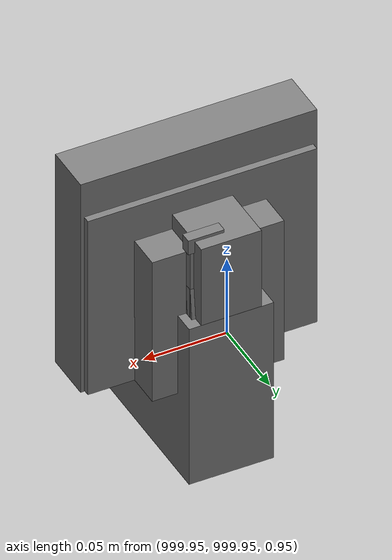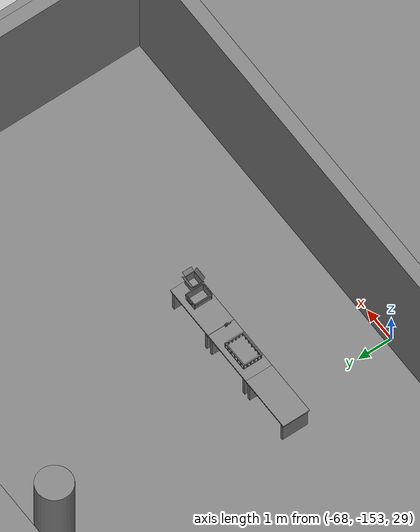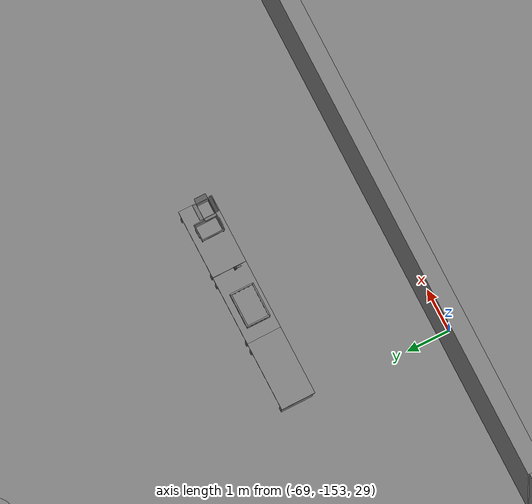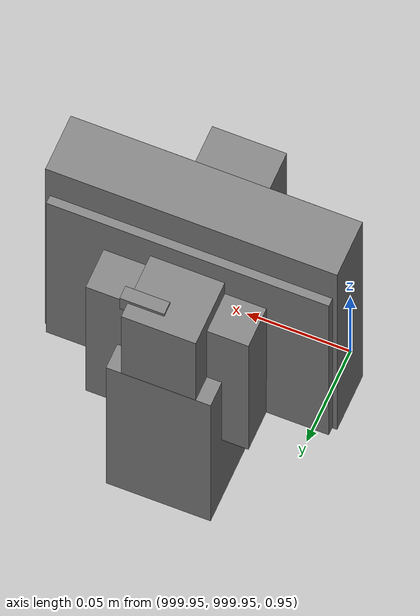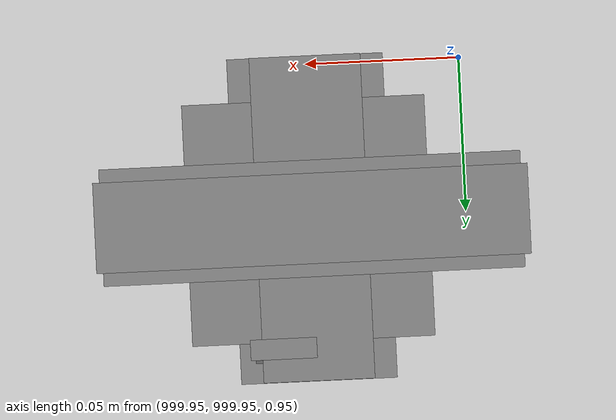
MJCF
<mujoco>
    <option gravity="0.000000000 0.000000000 -9.810000420" timestep="0.0049999999" integrator="implicitfast" density="1.225" viscosity="1.8000001e-05" noslip_iterations="10" iterations="100" sdf_iterations="50">
        <flag multiccd="disable"/>
    </option>
    <size memory="1000M"/>
    <compiler coordinate="local"/>
    <worldbody>
        <light cutoff="30" pos="0 1 1" dir="0 -1 -2"/>
        <light cutoff="30" pos="0 -1 1" dir="0 1 -2"/>
        <body pos="-64.866622925 -149.383972168 30.183746338" euler="89.999984741 89.999946594 0.000000000" name="openloong_gripper_2f85_fix_base_usda_bluebox_01">
            <geom contype="1" conaffinity="1" density="1000" type="box" material="" rgba="0.500000000 0.500000000 0.500000000 1.000000000" solimp="0.899999976 0.949999988 0.001000000" friction="1.000000000 0.005000000 0.000100000" solref="0.020000000 1.000000000" margin="0" condim="3" group="0" pos="0.276580811 0.187225342 0.000068665" quat="0.707106948 0.000077471 0.707106352 0.000077486" size="0.100000001 0.057999998 0.010000000" name="openloong_gripper_2f85_fix_base_usda_geom_BCC898AF_8036_46F1_8BF1_DBEEADE9F109"/>
            <geom contype="1" conaffinity="1" density="1000" type="box" material="" rgba="0.500000000 0.500000000 0.500000000 1.000000000" solimp="0.899999976 0.949999988 0.001000000" friction="1.000000000 0.005000000 0.000100000" solref="0.020000000 1.000000000" margin="0" condim="3" group="0" pos="0.000000000 0.002883911 0.000000000" quat="0.999999881 0.000000000 0.000000000 0.000000000" size="0.254000008 0.003000000 0.172000006" name="openloong_gripper_2f85_fix_base_usda_geom_5441E2D6_29DD_42C4_BC76_AA1399703A5B"/>
            <geom contype="1" conaffinity="1" density="1000" type="box" material="" rgba="0.500000000 0.500000000 0.500000000 1.000000000" solimp="0.899999976 0.949999988 0.001000000" friction="1.000000000 0.005000000 0.000100000" solref="0.020000000 1.000000000" margin="0" condim="3" group="0" pos="0.000000000 0.124874115 0.173484802" quat="0.999796331 0.020176515 -0.000000015 0.000000030" size="0.259999990 0.119999997 0.007000000" name="openloong_gripper_2f85_fix_base_usda_geom_A0157257_4676_4F60_934B_414192F5F17A"/>
            <geom contype="1" conaffinity="1" density="1000" type="box" material="" rgba="0.500000000 0.500000000 0.500000000 1.000000000" solimp="0.899999976 0.949999988 0.001000000" friction="1.000000000 0.005000000 0.000100000" solref="0.020000000 1.000000000" margin="0" condim="3" group="0" pos="0.000000000 0.124874115 -0.173469543" quat="0.999796331 -0.020176545 -0.000000015 0.000000000" size="0.259999990 0.119999997 0.007000000" name="openloong_gripper_2f85_fix_base_usda_geom_F7F46FCF_9DEA_456C_8797_1F9B75968A4C"/>
            <geom contype="1" conaffinity="1" density="1000" type="box" material="" rgba="0.500000000 0.500000000 0.500000000 1.000000000" solimp="0.899999976 0.949999988 0.001000000" friction="1.000000000 0.005000000 0.000100000" solref="0.020000000 1.000000000" margin="0" condim="3" group="0" pos="0.000000000 0.214008331 0.188980103" quat="0.999912977 0.013176724 0.000000015 0.000000000" size="0.259999990 0.029999999 0.012500000" name="openloong_gripper_2f85_fix_base_usda_geom_94E848E2_5716_4906_AA65_3BC5AE520784"/>
            <geom contype="1" conaffinity="1" density="1000" type="box" material="" rgba="0.500000000 0.500000000 0.500000000 1.000000000" solimp="0.899999976 0.949999988 0.001000000" friction="1.000000000 0.005000000 0.000100000" solref="0.020000000 1.000000000" margin="0" condim="3" group="0" pos="-0.258361816 0.125289917 0.001876831" quat="0.702796936 -0.020792112 0.710783124 0.020769298" size="0.189999998 0.119999997 0.009000000" name="openloong_gripper_2f85_fix_base_usda_geom_9DCEE43A_B328_48AA_A65E_06442B5DC2C4"/>
            <geom contype="1" conaffinity="1" density="1000" type="box" material="" rgba="0.500000000 0.500000000 0.500000000 1.000000000" solimp="0.899999976 0.949999988 0.001000000" friction="1.000000000 0.005000000 0.000100000" solref="0.020000000 1.000000000" margin="0" condim="3" group="0" pos="0.000000000 0.214008331 -0.188980103" quat="0.999912977 -0.013176769 0.000000030 0.000000015" size="0.259999990 0.029999999 0.012500000" name="openloong_gripper_2f85_fix_base_usda_geom_F73FC0EF_2E1D_4EE4_9E3D_F2566AD26DA3"/>
            <geom contype="1" conaffinity="1" density="1000" type="box" material="" rgba="0.500000000 0.500000000 0.500000000 1.000000000" solimp="0.899999976 0.949999988 0.001000000" friction="1.000000000 0.005000000 0.000100000" solref="0.020000000 1.000000000" margin="0" condim="3" group="0" pos="-0.276611328 0.187225342 0.000068665" quat="0.707106650 0.000077441 0.707106709 0.000077456" size="0.100000001 0.057999998 0.010000000" name="openloong_gripper_2f85_fix_base_usda_geom_A66D74AB_AFD8_4523_98D8_D843E9079168"/>
            <geom contype="1" conaffinity="1" density="1000" type="box" material="" rgba="0.500000000 0.500000000 0.500000000 1.000000000" solimp="0.899999976 0.949999988 0.001000000" friction="1.000000000 0.005000000 0.000100000" solref="0.020000000 1.000000000" margin="0" condim="3" group="0" pos="0.258331299 0.125289917 0.001876831" quat="0.702851415 0.018856421 0.710823774 -0.019329369" size="0.189999998 0.119999997 0.009000000" name="openloong_gripper_2f85_fix_base_usda_geom_9F8E9FC9_82B5_4382_A626_758942A28E05"/>
            <freejoint name="openloong_gripper_2f85_fix_base_usda_bluebox_01_joint"/>
            <site size="0.005000000 0.005000000 0.005000000" rgba="0.500000000 0.500000000 0.500000000 1.000000000" pos="0.000000000 0.000000000 0.000000000" quat="0.999961913 0.008726534 0.000000000 0.000000000" group="0" type="sphere" name="openloong_gripper_2f85_fix_base_usda_bluebox_01site"/>
        </body>
        <body pos="-64.496299744 -149.491867065 30.235729218" euler="0.000000000 0.000000000 89.999946594" name="openloong_gripper_2f85_fix_base_usda_cardboardbox_01">
            <geom contype="1" conaffinity="1" density="1000" type="box" material="" rgba="0.500000000 0.500000000 0.500000000 1.000000000" solimp="0.899999976 0.949999988 0.001000000" friction="1.000000000 0.005000000 0.000100000" solref="0.020000000 1.000000000" margin="0" condim="3" group="0" pos="-0.003166199 -0.004086494 0.005052090" quat="1.000000000 0.000000000 0.000000000 0.000000000" size="0.142499998 0.177500010 0.005000000" name="openloong_gripper_2f85_fix_base_usda_geom_9736E895_E666_453B_8FC5_706951A5FFA5"/>
            <geom contype="1" conaffinity="1" density="1000" type="box" material="" rgba="0.500000000 0.500000000 0.500000000 1.000000000" solimp="0.899999976 0.949999988 0.001000000" friction="1.000000000 0.005000000 0.000100000" solref="0.020000000 1.000000000" margin="0" condim="3" group="0" pos="-0.003166199 0.170316696 0.150570869" quat="1.000000000 0.000000000 0.000000000 0.000000000" size="0.142499998 0.005000000 0.149999991" name="openloong_gripper_2f85_fix_base_usda_geom_EE32C1CC_C0AE_42E8_8749_6D7BF7982EA7"/>
            <geom contype="1" conaffinity="1" density="1000" type="box" material="" rgba="0.500000000 0.500000000 0.500000000 1.000000000" solimp="0.899999976 0.949999988 0.001000000" friction="1.000000000 0.005000000 0.000100000" solref="0.020000000 1.000000000" margin="0" condim="3" group="0" pos="-0.147399902 -0.005307198 0.150570869" quat="1.000000000 0.000000000 0.000000000 0.000000000" size="0.005000000 0.177500010 0.149999991" name="openloong_gripper_2f85_fix_base_usda_geom_F9302DA8_764F_4684_8818_A9FB36A2CC14"/>
            <geom contype="1" conaffinity="1" density="1000" type="box" material="" rgba="0.500000000 0.500000000 0.500000000 1.000000000" solimp="0.899999976 0.949999988 0.001000000" friction="1.000000000 0.005000000 0.000100000" solref="0.020000000 1.000000000" margin="0" condim="3" group="0" pos="0.140275955 -0.005307198 0.150570869" quat="1.000000000 0.000000000 0.000000000 0.000000000" size="0.005000000 0.177500010 0.149999991" name="openloong_gripper_2f85_fix_base_usda_geom_5D86DADD_441B_4BA1_91F0_363AAB12D18D"/>
            <geom contype="1" conaffinity="1" density="1000" type="box" material="" rgba="0.500000000 0.500000000 0.500000000 1.000000000" solimp="0.899999976 0.949999988 0.001000000" friction="1.000000000 0.005000000 0.000100000" solref="0.020000000 1.000000000" margin="0" condim="3" group="0" pos="-0.003166199 -0.181550980 0.150570869" quat="1.000000000 0.000000000 0.000000000 0.000000000" size="0.142499998 0.005000000 0.149999991" name="openloong_gripper_2f85_fix_base_usda_geom_50F08D48_67F7_4B99_9BFD_C80CDF5DD982"/>
            <freejoint name="openloong_gripper_2f85_fix_base_usda_cardboardbox_01_joint"/>
            <site size="0.005000000 0.005000000 0.005000000" rgba="0.500000000 0.500000000 0.500000000 1.000000000" pos="0.000000000 0.000000000 0.000000000" quat="0.999961913 0.008726535 0.000000000 0.000000000" group="0" type="sphere" name="openloong_gripper_2f85_fix_base_usda_site_41AC9F1C_5248_469A_A939_DB9A5D9B8FB4"/>
            <body pos="0.139160156 -0.004048347 0.301930904" euler="-179.999954224 49.383502960 179.999954224" name="openloong_gripper_2f85_fix_base_usda_A1_006">
                <geom contype="1" conaffinity="1" density="1000" type="box" material="" rgba="0.500000000 0.500000000 0.500000000 1.000000000" solimp="0.899999976 0.949999988 0.001000000" friction="1.000000000 0.005000000 0.000100000" solref="0.020000000 1.000000000" margin="0" condim="3" group="0" pos="-0.071587563 0.000009537 0.001745224" quat="0.999999881 0.000000000 0.000000000 0.000000000" size="0.071249999 0.179999992 0.002500000" name="openloong_gripper_2f85_fix_base_usda_geom_D0AA1FB5_E3B8_40AC_9ADB_B52A653952B8"/>
                <joint armature="0" stiffness="0.07" damping="0.0099999998" axis="0.000000 1.000000 0.000000" type="hinge" name="openloong_gripper_2f85_fix_base_usda_A1_006"/>
            </body>
            <body pos="-0.145902634 -0.004086494 0.301938057" euler="-180.000000000 -60.000011444 -180.000000000" name="openloong_gripper_2f85_fix_base_usda_A2_006">
                <geom contype="1" conaffinity="1" density="1000" type="box" material="" rgba="0.500000000 0.500000000 0.500000000 1.000000000" solimp="0.899999976 0.949999988 0.001000000" friction="1.000000000 0.005000000 0.000100000" solref="0.020000000 1.000000000" margin="0" condim="3" group="0" pos="0.071268082 0.000009537 0.002717972" quat="0.000002921 0.000000000 -0.000000030 0.999999881" size="0.071249999 0.179999992 0.002500000" name="openloong_gripper_2f85_fix_base_usda_geom_0B552C2C_3ACC_468A_A98C_E4236E58712A"/>
                <joint armature="0" stiffness="0.07" damping="0.0099999998" axis="0.000000 1.000000 0.000000" type="hinge" name="openloong_gripper_2f85_fix_base_usda_A2_006"/>
            </body>
            <body pos="-0.003385544 0.175991058 0.301930904" euler="-125.858116150 -0.000004561 0.000002331" name="openloong_gripper_2f85_fix_base_usda_B2_006">
                <geom contype="1" conaffinity="1" density="1000" type="box" material="" rgba="0.500000000 0.500000000 0.500000000 1.000000000" solimp="0.899999976 0.949999988 0.001000000" friction="1.000000000 0.005000000 0.000100000" solref="0.020000000 1.000000000" margin="0" condim="3" group="0" pos="0.000009537 -0.070939064 -0.002470016" quat="0.999614120 0.027776197 -0.000000015 0.000000030" size="0.137500003 0.064999998 0.005000000" name="openloong_gripper_2f85_fix_base_usda_geom_B77B7AA8_CD89_4204_8D7D_9836E91ABF34"/>
                <joint armature="0" stiffness="0.07" damping="0.0099999998" axis="1.000000 0.000000 0.000000" type="hinge" name="openloong_gripper_2f85_fix_base_usda_B2_006"/>
            </body>
            <body pos="-0.003385544 -0.184140205 0.301938057" euler="147.805557251 0.000000000 0.000000000" name="openloong_gripper_2f85_fix_base_usda_B1_006">
                <geom contype="1" conaffinity="1" density="1000" type="box" material="" rgba="0.500000000 0.500000000 0.500000000 1.000000000" solimp="0.899999976 0.949999988 0.001000000" friction="1.000000000 0.005000000 0.000100000" solref="0.020000000 1.000000000" margin="0" condim="3" group="0" pos="-0.000028610 0.070202351 -0.002703667" quat="0.999614179 -0.027776167 0.000000000 0.000000000" size="0.137500003 0.064999998 0.005000000" name="openloong_gripper_2f85_fix_base_usda_geom_CE4ED5DD_846B_4105_84BF_C1CABF3307FA"/>
                <joint armature="0" stiffness="0.07" damping="0.0099999998" axis="1.000000 0.000000 0.000000" type="hinge" name="openloong_gripper_2f85_fix_base_usda_B1_006"/>
            </body>
        </body>
        <body pos="-65.882858276 -149.481979370 30.229999542" euler="-64.487716675 0.000000000 0.000000000" name="openloong_gripper_2f85_fix_base_usda_Barcode">
            <geom contype="1" conaffinity="1" density="1000" type="box" material="" rgba="0.500000000 0.500000000 0.500000000 1.000000000" solimp="0.899999976 0.949999988 0.001000000" friction="1.000000000 0.005000000 0.000100000" solref="0.020000000 1.000000000" margin="0" condim="3" group="0" pos="0.000000000 0.013038635 0.001419067" quat="0.000000000 0.000000000 0.000000000 1.000000119" size="0.034000002 0.010000000 0.017999999" name="openloong_gripper_2f85_fix_base_usda_geom_7CED0FCB_4A5F_404B_9A12_FCF1990164C3"/>
            <geom contype="1" conaffinity="1" density="1000" type="box" material="" rgba="0.500000000 0.500000000 0.500000000 1.000000000" solimp="0.899999976 0.949999988 0.001000000" friction="1.000000000 0.005000000 0.000100000" solref="0.020000000 1.000000000" margin="0" condim="3" group="0" pos="0.000000000 -0.035301208 -0.007095337" quat="0.000000000 0.000000000 -0.043619365 0.999048233" size="0.028999999 0.010000000 0.020000000" name="openloong_gripper_2f85_fix_base_usda_geom_282C615D_FA3D_4A03_9C30_9C280CFCBB8F"/>
            <geom contype="1" conaffinity="1" density="1000" type="box" material="" rgba="0.500000000 0.500000000 0.500000000 1.000000000" solimp="0.899999976 0.949999988 0.001000000" friction="1.000000000 0.005000000 0.000100000" solref="0.020000000 1.000000000" margin="0" condim="3" group="0" pos="0.000000000 -0.043411255 -0.011749268" quat="0.922262907 0.386563420 0.000000000 0.000000000" size="0.026000001 0.010000000 0.020000000" name="openloong_gripper_2f85_fix_base_usda_geom_941BFE28_1126_4463_8951_02606A02C98B"/>
            <geom contype="1" conaffinity="1" density="1000" type="box" material="" rgba="0.500000000 0.500000000 0.500000000 1.000000000" solimp="0.899999976 0.949999988 0.001000000" friction="1.000000000 0.005000000 0.000100000" solref="0.020000000 1.000000000" margin="0" condim="3" group="0" pos="0.000000000 -0.016967773 -0.031860352" quat="0.000000000 0.000000000 0.000000000 1.000000119" size="0.008000000 0.010000000 0.013000000" name="openloong_gripper_2f85_fix_base_usda_geom_2FFE92EA_04A9_44B3_956A_B1D4AA8AD8B6"/>
            <geom contype="1" conaffinity="1" density="1000" type="box" material="" rgba="0.500000000 0.500000000 0.500000000 1.000000000" solimp="0.899999976 0.949999988 0.001000000" friction="1.000000000 0.005000000 0.000100000" solref="0.020000000 1.000000000" margin="0" condim="3" group="0" pos="0.000000000 -0.001869202 0.000312805" quat="0.953716993 0.300705761 0.000000000 0.000000000" size="0.032000002 0.010000000 0.018999999" name="openloong_gripper_2f85_fix_base_usda_geom_E105EB1C_A677_49C8_B2C8_D506991C15D9"/>
            <geom contype="1" conaffinity="1" density="1000" type="box" material="" rgba="0.500000000 0.500000000 0.500000000 1.000000000" solimp="0.899999976 0.949999988 0.001000000" friction="1.000000000 0.005000000 0.000100000" solref="0.020000000 1.000000000" margin="0" condim="3" group="0" pos="0.000000000 -0.019531250 -0.003173828" quat="0.953716993 0.300705761 0.000000000 0.000000000" size="0.030999999 0.010000000 0.020000000" name="openloong_gripper_2f85_fix_base_usda_geom_8F45C6C0_7780_4A36_930F_340351C7B829"/>
            <geom contype="1" conaffinity="1" density="1000" type="box" material="" rgba="0.500000000 0.500000000 0.500000000 1.000000000" solimp="0.899999976 0.949999988 0.001000000" friction="1.000000000 0.005000000 0.000100000" solref="0.020000000 1.000000000" margin="0" condim="3" group="0" pos="0.000000000 -0.035301208 -0.007095337" quat="0.953716993 0.300705761 0.000000000 0.000000000" size="0.028999999 0.010000000 0.020000000" name="openloong_gripper_2f85_fix_base_usda_geom_17600BB0_A6F4_4046_85DA_E97A77B4B749"/>
            <geom contype="1" conaffinity="1" density="1000" type="box" material="" rgba="0.500000000 0.500000000 0.500000000 1.000000000" solimp="0.899999976 0.949999988 0.001000000" friction="1.000000000 0.005000000 0.000100000" solref="0.020000000 1.000000000" margin="0" condim="3" group="0" pos="0.000000000 -0.042617798 -0.071121216" quat="0.000000000 0.000000000 0.000000000 1.000000119" size="0.013000000 0.021000000 0.059999999" name="openloong_gripper_2f85_fix_base_usda_geom_7D71C9AA_764C_4FE0_9A3E_BDA20F036816"/>
            <freejoint name="openloong_gripper_2f85_fix_base_usda_Barcode_joint"/>
            <site size="0.005000000 0.005000000 0.005000000" rgba="0.500000000 0.500000000 0.500000000 1.000000000" pos="0.000000000 0.000000000 0.000000000" quat="1.000000000 0.000000000 0.000000000 0.000000000" group="0" type="sphere" name="openloong_gripper_2f85_fix_base_usda_Barcode_site"/>
        </body>
        <body pos="-66.745018005 -149.392349243 30.184000015" euler="0.000000000 0.000000000 89.999946594" name="[22330870595997]_Basket_01">
            <geom contype="1" conaffinity="1" density="1000" type="box" material="" rgba="0.500000000 0.500000000 0.500000000 1.000000000" solimp="0.899999976 0.949999988 0.001000000" friction="1.000000000 0.005000000 0.000100000" solref="0.020000000 1.000000000" margin="0" condim="3" group="0" pos="-0.052425385 0.389207840 0.089787483" quat="0.707107008 0.000000000 0.000000000 0.707106411" size="0.014249999 0.014249999 0.059999999" name="[22330870595997]_geom_06F5A53B_7710_409C_93B6_74631413C62F"/>
            <geom contype="1" conaffinity="1" density="1000" type="box" material="" rgba="0.500000000 0.500000000 0.500000000 1.000000000" solimp="0.899999976 0.949999988 0.001000000" friction="1.000000000 0.005000000 0.000100000" solref="0.020000000 1.000000000" margin="0" condim="3" group="0" pos="0.264015198 -0.133043289 0.089787483" quat="0.707107008 0.000000000 0.000000000 0.707106411" size="0.014249999 0.014249999 0.059999999" name="[22330870595997]_geom_1C625842_EFFD_41CB_90FC_910B56AFD099"/>
            <geom contype="1" conaffinity="1" density="1000" type="box" material="" rgba="0.500000000 0.500000000 0.500000000 1.000000000" solimp="0.899999976 0.949999988 0.001000000" friction="1.000000000 0.005000000 0.000100000" solref="0.020000000 1.000000000" margin="0" condim="3" group="0" pos="-0.264015198 -0.265548706 0.089793205" quat="0.707107008 0.000000000 0.000000000 0.707106411" size="0.014249999 0.014249999 0.059999999" name="[22330870595997]_geom_0C992FC0_5BA0_493A_BE18_934D84C02134"/>
            <geom contype="1" conaffinity="1" density="1000" type="box" material="" rgba="0.500000000 0.500000000 0.500000000 1.000000000" solimp="0.899999976 0.949999988 0.001000000" friction="1.000000000 0.005000000 0.000100000" solref="0.020000000 1.000000000" margin="0" condim="3" group="0" pos="-0.160263062 -0.389322281 0.089793205" quat="0.707107008 0.000000000 0.000000000 0.707106411" size="0.014249999 0.014249999 0.059999999" name="[22330870595997]_geom_679BB005_7817_4FDC_ADE0_39E38C087338"/>
            <geom contype="1" conaffinity="1" density="1000" type="box" material="" rgba="0.500000000 0.500000000 0.500000000 1.000000000" solimp="0.899999976 0.949999988 0.001000000" friction="1.000000000 0.005000000 0.000100000" solref="0.020000000 1.000000000" margin="0" condim="3" group="0" pos="0.162265778 -0.389322281 0.089787483" quat="0.707107008 0.000000000 0.000000000 0.707106411" size="0.014249999 0.014249999 0.059999999" name="[22330870595997]_geom_3175E497_9E1C_4C21_AB79_479B9CB98FA4"/>
            <geom contype="1" conaffinity="1" density="1000" type="box" material="" rgba="0.500000000 0.500000000 0.500000000 1.000000000" solimp="0.899999976 0.949999988 0.001000000" friction="1.000000000 0.005000000 0.000100000" solref="0.020000000 1.000000000" margin="0" condim="3" group="0" pos="0.264015198 0.389207840 0.089787483" quat="0.707107008 0.000000000 0.000000000 0.707106411" size="0.014249999 0.014249999 0.059999999" name="[22330870595997]_geom_369ED3B7_635B_404A_B611_33775C395303"/>
            <geom contype="1" conaffinity="1" density="1000" type="box" material="" rgba="0.500000000 0.500000000 0.500000000 1.000000000" solimp="0.899999976 0.949999988 0.001000000" friction="1.000000000 0.005000000 0.000100000" solref="0.020000000 1.000000000" margin="0" condim="3" group="0" pos="-0.264015198 -0.133043289 0.089793205" quat="0.707107008 0.000000000 0.000000000 0.707106411" size="0.014249999 0.014249999 0.059999999" name="[22330870595997]_geom_2796B62F_67A5_4D74_A4CF_FDC1F4DC247A"/>
            <geom contype="1" conaffinity="1" density="1000" type="box" material="" rgba="0.500000000 0.500000000 0.500000000 1.000000000" solimp="0.899999976 0.949999988 0.001000000" friction="1.000000000 0.005000000 0.000100000" solref="0.020000000 1.000000000" margin="0" condim="3" group="0" pos="-0.264026642 0.269256592 0.089793205" quat="0.707107008 0.000000000 0.000000000 0.707106411" size="0.014249999 0.014249999 0.059999999" name="[22330870595997]_geom_4D24A4C5_BDE8_448A_9836_79896AC99974"/>
            <geom contype="1" conaffinity="1" density="1000" type="box" material="" rgba="0.500000000 0.500000000 0.500000000 1.000000000" solimp="0.899999976 0.949999988 0.001000000" friction="1.000000000 0.005000000 0.000100000" solref="0.020000000 1.000000000" margin="0" condim="3" group="0" pos="0.054462433 0.389207840 0.089787483" quat="0.707107008 0.000000000 0.000000000 0.707106411" size="0.014249999 0.014249999 0.059999999" name="[22330870595997]_geom_32335410_1D04_475F_87FF_27B1A491F44A"/>
            <geom contype="1" conaffinity="1" density="1000" type="box" material="" rgba="0.500000000 0.500000000 0.500000000 1.000000000" solimp="0.899999976 0.949999988 0.001000000" friction="1.000000000 0.005000000 0.000100000" solref="0.020000000 1.000000000" margin="0" condim="3" group="0" pos="0.054462433 -0.389322281 0.089787483" quat="0.707107008 0.000000000 0.000000000 0.707106411" size="0.014249999 0.014249999 0.059999999" name="[22330870595997]_geom_C99E37A9_4BD9_40E1_8D8C_0F3F95BECC70"/>
            <geom contype="1" conaffinity="1" density="1000" type="box" material="" rgba="0.500000000 0.500000000 0.500000000 1.000000000" solimp="0.899999976 0.949999988 0.001000000" friction="1.000000000 0.005000000 0.000100000" solref="0.020000000 1.000000000" margin="0" condim="3" group="0" pos="0.264015198 0.269256592 0.089793205" quat="0.707107008 0.000000000 0.000000000 0.707106411" size="0.014249999 0.014249999 0.059999999" name="[22330870595997]_geom_6C1ED2FA_76CA_4D0A_AA18_73DC4B61272C"/>
            <geom contype="1" conaffinity="1" density="1000" type="box" material="" rgba="0.500000000 0.500000000 0.500000000 1.000000000" solimp="0.899999976 0.949999988 0.001000000" friction="1.000000000 0.005000000 0.000100000" solref="0.020000000 1.000000000" margin="0" condim="3" group="0" pos="0.264015198 -0.389322281 0.089787483" quat="0.707107008 0.000000000 0.000000000 0.707106411" size="0.014249999 0.014249999 0.059999999" name="[22330870595997]_geom_C44DC115_8D94_43C1_BB85_BCE938D24ED2"/>
            <geom contype="1" conaffinity="1" density="1000" type="box" material="" rgba="0.500000000 0.500000000 0.500000000 1.000000000" solimp="0.899999976 0.949999988 0.001000000" friction="1.000000000 0.005000000 0.000100000" solref="0.020000000 1.000000000" margin="0" condim="3" group="0" pos="0.000000000 0.000000000 0.015998840" quat="0.707107008 0.000000000 0.000000000 0.707106411" size="0.403499991 0.279000014 0.015750000" name="[22330870595997]_geom_529A56AE_7334_4932_A98B_C461E1811A09"/>
            <geom contype="1" conaffinity="1" density="1000" type="box" material="" rgba="0.500000000 0.500000000 0.500000000 1.000000000" solimp="0.899999976 0.949999988 0.001000000" friction="1.000000000 0.005000000 0.000100000" solref="0.020000000 1.000000000" margin="0" condim="3" group="0" pos="0.000000000 -0.389476776 0.163619041" quat="0.707107008 0.000000000 0.000000000 0.707106411" size="0.015000000 0.277500004 0.015750000" name="[22330870595997]_geom_A9DB3232_74EE_4D02_9E14_F80052C10055"/>
            <geom contype="1" conaffinity="1" density="1000" type="box" material="" rgba="0.500000000 0.500000000 0.500000000 1.000000000" solimp="0.899999976 0.949999988 0.001000000" friction="1.000000000 0.005000000 0.000100000" solref="0.020000000 1.000000000" margin="0" condim="3" group="0" pos="0.162265778 0.389207840 0.089787483" quat="0.707107008 0.000000000 0.000000000 0.707106411" size="0.014249999 0.014249999 0.059999999" name="[22330870595997]_geom_554208FC_5263_4E4D_BA10_83047E47B6B3"/>
            <geom contype="1" conaffinity="1" density="1000" type="box" material="" rgba="0.500000000 0.500000000 0.500000000 1.000000000" solimp="0.899999976 0.949999988 0.001000000" friction="1.000000000 0.005000000 0.000100000" solref="0.020000000 1.000000000" margin="0" condim="3" group="0" pos="0.000000000 0.389471054 0.163619041" quat="0.707107008 0.000000000 0.000000000 0.707106411" size="0.015000000 0.277500004 0.015750000" name="[22330870595997]_geom_8D1427B6_B842_4C95_BFBA_94DBFC3915AD"/>
            <geom contype="1" conaffinity="1" density="1000" type="box" material="" rgba="0.500000000 0.500000000 0.500000000 1.000000000" solimp="0.899999976 0.949999988 0.001000000" friction="1.000000000 0.005000000 0.000100000" solref="0.020000000 1.000000000" margin="0" condim="3" group="0" pos="-0.263511658 0.000000000 0.163619041" quat="0.707107008 0.000000000 0.000000000 0.707106411" size="0.403499991 0.015000000 0.015750000" name="[22330870595997]_geom_87E80BF6_FD6D_448A_A038_6FDBE9958F07"/>
            <geom contype="1" conaffinity="1" density="1000" type="box" material="" rgba="0.500000000 0.500000000 0.500000000 1.000000000" solimp="0.899999976 0.949999988 0.001000000" friction="1.000000000 0.005000000 0.000100000" solref="0.020000000 1.000000000" margin="0" condim="3" group="0" pos="-0.264015198 0.141334534 0.089793205" quat="0.707107008 0.000000000 0.000000000 0.707106411" size="0.014249999 0.014249999 0.059999999" name="[22330870595997]_geom_98767344_28D2_484E_A58A_1213DF7579C4"/>
            <geom contype="1" conaffinity="1" density="1000" type="box" material="" rgba="0.500000000 0.500000000 0.500000000 1.000000000" solimp="0.899999976 0.949999988 0.001000000" friction="1.000000000 0.005000000 0.000100000" solref="0.020000000 1.000000000" margin="0" condim="3" group="0" pos="0.264015198 -0.265548706 0.089787483" quat="0.707107008 0.000000000 0.000000000 0.707106411" size="0.014249999 0.014249999 0.059999999" name="[22330870595997]_geom_500274D3_2D19_4292_B067_CBDD0B106E62"/>
            <geom contype="1" conaffinity="1" density="1000" type="box" material="" rgba="0.500000000 0.500000000 0.500000000 1.000000000" solimp="0.899999976 0.949999988 0.001000000" friction="1.000000000 0.005000000 0.000100000" solref="0.020000000 1.000000000" margin="0" condim="3" group="0" pos="-0.160263062 0.389207840 0.089787483" quat="0.707107008 0.000000000 0.000000000 0.707106411" size="0.014249999 0.014249999 0.059999999" name="[22330870595997]_geom_8E0309ED_5023_485E_9E35_BBD437F6AD74"/>
            <geom contype="1" conaffinity="1" density="1000" type="box" material="" rgba="0.500000000 0.500000000 0.500000000 1.000000000" solimp="0.899999976 0.949999988 0.001000000" friction="1.000000000 0.005000000 0.000100000" solref="0.020000000 1.000000000" margin="0" condim="3" group="0" pos="-0.052425385 -0.389322281 0.089787483" quat="0.707107008 0.000000000 0.000000000 0.707106411" size="0.014249999 0.014249999 0.059999999" name="[22330870595997]_geom_DF0C139F_CDFE_48CE_AF84_620A76883A7D"/>
            <geom contype="1" conaffinity="1" density="1000" type="box" material="" rgba="0.500000000 0.500000000 0.500000000 1.000000000" solimp="0.899999976 0.949999988 0.001000000" friction="1.000000000 0.005000000 0.000100000" solref="0.020000000 1.000000000" margin="0" condim="3" group="0" pos="-0.264026642 -0.389322281 0.089793205" quat="0.707107008 0.000000000 0.000000000 0.707106411" size="0.014249999 0.014249999 0.059999999" name="[22330870595997]_geom_D311B3AC_0E99_4FCA_8D6E_CEC1AF015E8E"/>
            <geom contype="1" conaffinity="1" density="1000" type="box" material="" rgba="0.500000000 0.500000000 0.500000000 1.000000000" solimp="0.899999976 0.949999988 0.001000000" friction="1.000000000 0.005000000 0.000100000" solref="0.020000000 1.000000000" margin="0" condim="3" group="0" pos="0.264015198 0.141334534 0.089787483" quat="0.707107008 0.000000000 0.000000000 0.707106411" size="0.014249999 0.014249999 0.059999999" name="[22330870595997]_geom_25D1683B_63E8_4BA4_BB31_E8B1564F7434"/>
            <geom contype="1" conaffinity="1" density="1000" type="box" material="" rgba="0.500000000 0.500000000 0.500000000 1.000000000" solimp="0.899999976 0.949999988 0.001000000" friction="1.000000000 0.005000000 0.000100000" solref="0.020000000 1.000000000" margin="0" condim="3" group="0" pos="-0.264015198 0.389207840 0.089793205" quat="0.707107008 0.000000000 0.000000000 0.707106411" size="0.014249999 0.014249999 0.059999999" name="[22330870595997]_geom_EF035804_C0B2_48DD_8862_E128A644DE14"/>
            <geom contype="1" conaffinity="1" density="1000" type="box" material="" rgba="0.500000000 0.500000000 0.500000000 1.000000000" solimp="0.899999976 0.949999988 0.001000000" friction="1.000000000 0.005000000 0.000100000" solref="0.020000000 1.000000000" margin="0" condim="3" group="0" pos="0.264015198 0.004480362 0.089787483" quat="0.707107008 0.000000000 0.000000000 0.707106411" size="0.014249999 0.014249999 0.059999999" name="[22330870595997]_geom_71DCBAC0_B032_4465_8534_B61EC4C77B4E"/>
            <geom contype="1" conaffinity="1" density="1000" type="box" material="" rgba="0.500000000 0.500000000 0.500000000 1.000000000" solimp="0.899999976 0.949999988 0.001000000" friction="1.000000000 0.005000000 0.000100000" solref="0.020000000 1.000000000" margin="0" condim="3" group="0" pos="0.263694763 -0.000011444 0.163619041" quat="0.707107008 0.000000000 0.000000000 0.707106411" size="0.403499991 0.015000000 0.015750000" name="[22330870595997]_geom_4BA98978_E89C_467A_84E6_696E4D93DB2E"/>
            <geom contype="1" conaffinity="1" density="1000" type="box" material="" rgba="0.500000000 0.500000000 0.500000000 1.000000000" solimp="0.899999976 0.949999988 0.001000000" friction="1.000000000 0.005000000 0.000100000" solref="0.020000000 1.000000000" margin="0" condim="3" group="0" pos="-0.264015198 0.004480362 0.089793205" quat="0.707107008 0.000000000 0.000000000 0.707106411" size="0.014249999 0.014249999 0.059999999" name="[22330870595997]_geom_7D9403FA_7937_4C32_A6E4_7B29550A4EFA"/>
            <freejoint name="[22330870595997]_joint_4D4BD2A6_485B_438C_9F3E_1E37FE9C1F5A"/>
        </body>
        <body pos="0.000000000 0.000000000 0.000000000" euler="0.000000000 0.000000000 0.000000000" name="Static Objects_Static Objects">
            <geom contype="1" conaffinity="1" density="1000" type="box" material="" rgba="0.500000000 0.500000000 0.500000000 1.000000000" solimp="0.899999976 0.949999988 0.001000000" friction="1.000000000 0.005000000 0.000100000" solref="0.020000000 1.000000000" margin="0" condim="3" group="0" pos="-67.544113159 -149.365814209 29.727830887" quat="0.500000417 0.499999970 0.499999553 0.499999970" size="0.381000012 0.319999993 0.041000001" name="Static Objects_geom_46CF15D4_E0BD_4C8C_9330_F741B644E804"/>
            <geom contype="1" conaffinity="1" density="1000" type="box" material="" rgba="0.500000000 0.500000000 0.500000000 1.000000000" solimp="0.899999976 0.949999988 0.001000000" friction="1.000000000 0.005000000 0.000100000" solref="0.020000000 1.000000000" margin="0" condim="3" group="0" pos="-68.239501953 -149.365814209 30.086868286" quat="0.500000417 0.499999970 0.499999553 0.499999970" size="0.370999992 0.039500002 0.745000005" name="Static Objects_geom_BC20104D_E0B3_42D0_A8D7_A8BD669AAB55"/>
            <geom contype="1" conaffinity="1" density="1000" type="box" material="" rgba="0.500000000 0.500000000 0.500000000 1.000000000" solimp="0.899999976 0.949999988 0.001000000" friction="1.000000000 0.005000000 0.000100000" solref="0.020000000 1.000000000" margin="0" condim="3" group="0" pos="-68.239501953 -149.365814209 30.147235870" quat="0.500000417 0.499999970 0.499999553 0.499999970" size="0.400000006 0.022000000 0.800000012" name="Static Objects_geom_54661DEC_5C71_4D34_B1FA_A612A956D922"/>
            <geom contype="1" conaffinity="1" density="1000" type="box" material="" rgba="0.500000000 0.500000000 0.500000000 1.000000000" solimp="0.899999976 0.949999988 0.001000000" friction="1.000000000 0.005000000 0.000100000" solref="0.020000000 1.000000000" margin="0" condim="3" group="0" pos="-68.934890747 -149.365814209 29.727830887" quat="0.500000417 0.499999970 0.499999553 0.499999970" size="0.381000012 0.319999993 0.041000001" name="Static Objects_geom_47603673_294A_451D_AAF5_49BD351F617F"/>
            <geom contype="1" conaffinity="1" density="1000" type="box" material="" rgba="0.500000000 0.500000000 0.500000000 1.000000000" solimp="0.899999976 0.949999988 0.001000000" friction="1.000000000 0.005000000 0.000100000" solref="0.020000000 1.000000000" margin="0" condim="3" group="0" pos="-68.239501953 -149.365814209 29.561563492" quat="0.500000417 0.499999970 0.499999553 0.499999970" size="0.020000000 0.022000000 0.660000026" name="Static Objects_geom_20DFFDA1_F7EF_4F7C_B205_C25524624BED"/>
            <geom contype="1" conaffinity="1" density="1000" type="box" material="" rgba="0.500000000 0.500000000 0.500000000 1.000000000" solimp="0.899999976 0.949999988 0.001000000" friction="1.000000000 0.005000000 0.000100000" solref="0.020000000 1.000000000" margin="0" condim="3" group="0" pos="-65.945671082 -149.365814209 29.727830887" quat="0.500000417 0.499999970 0.499999553 0.499999970" size="0.381000012 0.319999993 0.041000001" name="Static Objects_geom_C0318369_9062_4800_B91D_D8B6D4798A1F"/>
            <geom contype="1" conaffinity="1" density="1000" type="box" material="" rgba="0.500000000 0.500000000 0.500000000 1.000000000" solimp="0.899999976 0.949999988 0.001000000" friction="1.000000000 0.005000000 0.000100000" solref="0.020000000 1.000000000" margin="0" condim="3" group="0" pos="-66.641059875 -149.365814209 30.086868286" quat="0.500000417 0.499999970 0.499999553 0.499999970" size="0.370999992 0.039500002 0.745000005" name="Static Objects_geom_53FACEA6_4D66_4A64_9FBC_90918FA3D215"/>
            <geom contype="1" conaffinity="1" density="1000" type="box" material="" rgba="0.500000000 0.500000000 0.500000000 1.000000000" solimp="0.899999976 0.949999988 0.001000000" friction="1.000000000 0.005000000 0.000100000" solref="0.020000000 1.000000000" margin="0" condim="3" group="0" pos="-66.641059875 -149.365814209 30.147235870" quat="0.500000417 0.499999970 0.499999553 0.499999970" size="0.400000006 0.022000000 0.800000012" name="Static Objects_geom_E3F0668C_F2BE_4318_8C93_4386AAAB38D0"/>
            <geom contype="1" conaffinity="1" density="1000" type="box" material="" rgba="0.500000000 0.500000000 0.500000000 1.000000000" solimp="0.899999976 0.949999988 0.001000000" friction="1.000000000 0.005000000 0.000100000" solref="0.020000000 1.000000000" margin="0" condim="3" group="0" pos="-67.336448669 -149.365814209 29.727830887" quat="0.500000417 0.499999970 0.499999553 0.499999970" size="0.381000012 0.319999993 0.041000001" name="Static Objects_geom_2E65518E_C36F_4761_9811_6D1C77262ED6"/>
            <geom contype="1" conaffinity="1" density="1000" type="box" material="" rgba="0.500000000 0.500000000 0.500000000 1.000000000" solimp="0.899999976 0.949999988 0.001000000" friction="1.000000000 0.005000000 0.000100000" solref="0.020000000 1.000000000" margin="0" condim="3" group="0" pos="-66.641059875 -149.365814209 29.561563492" quat="0.500000417 0.499999970 0.499999553 0.499999970" size="0.020000000 0.022000000 0.660000026" name="Static Objects_geom_463CACA5_D9C2_4414_9A47_B1AAA8CB1089"/>
            <geom contype="1" conaffinity="1" density="1000" type="box" material="" rgba="0.500000000 0.500000000 0.500000000 1.000000000" solimp="0.899999976 0.949999988 0.001000000" friction="1.000000000 0.005000000 0.000100000" solref="0.020000000 1.000000000" margin="0" condim="3" group="0" pos="-64.338577271 -149.365814209 29.727830887" quat="0.500000417 0.499999970 0.499999553 0.499999970" size="0.381000012 0.319999993 0.041000001" name="Static Objects_geom_83848E83_8B8E_44CC_8139_04BEB6DC7E20"/>
            <geom contype="1" conaffinity="1" density="1000" type="box" material="" rgba="0.500000000 0.500000000 0.500000000 1.000000000" solimp="0.899999976 0.949999988 0.001000000" friction="1.000000000 0.005000000 0.000100000" solref="0.020000000 1.000000000" margin="0" condim="3" group="0" pos="-65.033966064 -149.365814209 30.086868286" quat="0.500000417 0.499999970 0.499999553 0.499999970" size="0.370999992 0.039500002 0.745000005" name="Static Objects_geom_986A0792_AF24_4EC1_9B7E_700AF007B478"/>
            <geom contype="1" conaffinity="1" density="1000" type="box" material="" rgba="0.500000000 0.500000000 0.500000000 1.000000000" solimp="0.899999976 0.949999988 0.001000000" friction="1.000000000 0.005000000 0.000100000" solref="0.020000000 1.000000000" margin="0" condim="3" group="0" pos="-65.033966064 -149.365814209 30.147235870" quat="0.500000417 0.499999970 0.499999553 0.499999970" size="0.400000006 0.022000000 0.800000012" name="Static Objects_geom_8D42CDF4_8D65_4CCA_9A8C_71B75E5B4CB1"/>
            <geom contype="1" conaffinity="1" density="1000" type="box" material="" rgba="0.500000000 0.500000000 0.500000000 1.000000000" solimp="0.899999976 0.949999988 0.001000000" friction="1.000000000 0.005000000 0.000100000" solref="0.020000000 1.000000000" margin="0" condim="3" group="0" pos="-65.729354858 -149.365814209 29.727830887" quat="0.500000417 0.499999970 0.499999553 0.499999970" size="0.381000012 0.319999993 0.041000001" name="Static Objects_geom_F3E97B83_B543_4DEA_87EE_24A6F15EACE7"/>
            <geom contype="1" conaffinity="1" density="1000" type="box" material="" rgba="0.500000000 0.500000000 0.500000000 1.000000000" solimp="0.899999976 0.949999988 0.001000000" friction="1.000000000 0.005000000 0.000100000" solref="0.020000000 1.000000000" margin="0" condim="3" group="0" pos="-65.033966064 -149.365814209 29.561563492" quat="0.500000417 0.499999970 0.499999553 0.499999970" size="0.020000000 0.022000000 0.660000026" name="Static Objects_geom_1ADBF844_1306_4BE3_AAE1_63B9BD711366"/>
            <geom contype="1" conaffinity="1" density="1000" type="box" material="" rgba="0.500000000 0.500000000 0.500000000 1.000000000" solimp="0.899999976 0.949999988 0.001000000" friction="1.000000000 0.005000000 0.000100000" solref="0.020000000 1.000000000" margin="0" condim="3" group="0" pos="-61.754566193 -137.853729248 33.906845093" quat="0.707107067 0.000000000 0.000000000 0.707106471" size="0.759999990 0.759999990 4.500000000" name="Static Objects_geom_B5C32128_942F_4467_ADDA_9364B87FEFDF"/>
            <geom contype="1" conaffinity="1" density="1000" type="box" material="" rgba="0.500000000 0.500000000 0.500000000 1.000000000" solimp="0.899999976 0.949999988 0.001000000" friction="1.000000000 0.005000000 0.000100000" solref="0.020000000 1.000000000" margin="0" condim="3" group="0" pos="-57.511135101 -144.927108765 31.707921982" quat="1.000000000 0.000000000 0.000000000 0.000000000" size="0.200000003 8.000000000 2.299999952" name="Static Objects_geom_4456E17D_B050_4E75_A68D_19622071B318"/>
            <geom contype="1" conaffinity="1" density="1000" type="box" material="" rgba="0.500000000 0.500000000 0.500000000 1.000000000" solimp="0.899999976 0.949999988 0.001000000" friction="1.000000000 0.005000000 0.000100000" solref="0.020000000 1.000000000" margin="0" condim="3" group="0" pos="-80.517646790 -157.574050903 31.688196182" quat="0.707107067 0.000000000 0.000000000 0.707106471" size="0.600000024 0.600000024 2.299999952" name="Static Objects_geom_B6796BDD_076E_4300_A432_31BBB56F9D9D"/>
            <geom contype="1" conaffinity="1" density="1000" type="box" material="" rgba="0.500000000 0.500000000 0.500000000 1.000000000" solimp="0.899999976 0.949999988 0.001000000" friction="1.000000000 0.005000000 0.000100000" solref="0.020000000 1.000000000" margin="0" condim="3" group="0" pos="-80.711044312 -147.414932251 31.666158676" quat="1.000000000 0.000000000 0.000000000 0.000000000" size="0.200000003 10.000000000 2.299999952" name="Static Objects_geom_4D497AE6_3C58_4806_B40B_AD84DEB3770E"/>
            <geom contype="1" conaffinity="1" density="1000" type="box" material="" rgba="0.500000000 0.500000000 0.500000000 1.000000000" solimp="0.899999976 0.949999988 0.001000000" friction="1.000000000 0.005000000 0.000100000" solref="0.020000000 1.000000000" margin="0" condim="3" group="0" pos="-57.687217712 -137.434692383 31.688196182" quat="0.707107067 0.000000000 0.000000000 0.707106471" size="0.600000024 0.600000024 2.299999952" name="Static Objects_geom_B582AD87_167B_4F32_A65C_7DB2835ED190"/>
            <geom contype="1" conaffinity="1" density="1000" type="box" material="" rgba="0.500000000 0.500000000 0.500000000 1.000000000" solimp="0.899999976 0.949999988 0.001000000" friction="1.000000000 0.005000000 0.000100000" solref="0.020000000 1.000000000" margin="0" condim="3" group="0" pos="-69.537033081 -140.263229370 31.714921951" quat="0.707107067 0.000000000 0.000000000 0.707106471" size="0.759999990 4.500000000 2.299999952" name="Static Objects_geom_E48742CF_0E9E_4F08_8947_090BC9232F4B"/>
            <geom contype="1" conaffinity="1" density="1000" type="box" material="" rgba="0.500000000 0.500000000 0.500000000 1.000000000" solimp="0.899999976 0.949999988 0.001000000" friction="1.000000000 0.005000000 0.000100000" solref="0.020000000 1.000000000" margin="0" condim="3" group="0" pos="-80.073638916 -137.853713989 33.906845093" quat="0.707107067 0.000000000 0.000000000 0.707106471" size="0.759999990 0.759999990 4.500000000" name="Static Objects_geom_4BA0E431_F82B_4985_957D_0DDE43A1543D"/>
            <geom contype="1" conaffinity="1" density="1000" type="box" material="" rgba="0.500000000 0.500000000 0.500000000 1.000000000" solimp="0.899999976 0.949999988 0.001000000" friction="1.000000000 0.005000000 0.000100000" solref="0.020000000 1.000000000" margin="0" condim="3" group="0" pos="-73.406707764 -155.734664917 31.707921982" quat="1.000000000 0.000000000 0.000000000 0.000000000" size="0.200000003 3.000000000 2.299999952" name="Static Objects_geom_A13787BA_7A27_4ADC_BA37_F3F915F7C654"/>
            <geom contype="1" conaffinity="1" density="1000" type="box" material="" rgba="0.500000000 0.500000000 0.500000000 1.000000000" solimp="0.899999976 0.949999988 0.001000000" friction="1.000000000 0.005000000 0.000100000" solref="0.020000000 1.000000000" margin="0" condim="3" group="0" pos="-68.497543335 -137.448257446 31.707921982" quat="0.707107067 0.000000000 0.000000000 0.707106471" size="0.200000003 14.000000000 2.299999952" name="Static Objects_geom_2CE62FD4_BCF2_4E3A_8290_AB523D672DDE"/>
            <geom contype="1" conaffinity="1" density="1000" type="cylinder" material="" rgba="0.500000000 0.500000000 0.500000000 1.000000000" solimp="0.899999976 0.949999988 0.001000000" friction="1.000000000 0.005000000 0.000100000" solref="0.020000000 1.000000000" margin="0" condim="3" group="0" pos="-68.868522644 -142.134506226 31.711090088" quat="0.707107067 0.000000000 0.000000000 0.707106471" size="0.509999990 2.299999952 1.000000000" name="Static Objects_geom_E09DD495_B924_4921_9D38_ED50DE164F59"/>
            <geom contype="1" conaffinity="1" density="1000" type="plane" material="" rgba="0.500000000 0.500000000 0.500000000 1.000000000" solimp="0.899999976 0.949999988 0.001000000" friction="1.000000000 0.005000000 0.000100000" solref="0.020000000 1.000000000" margin="0" condim="3" group="0" pos="-72.873703003 -147.131927490 29.409669876" quat="1.000000000 0.000000000 0.000000000 0.000000000" size="18.000000000 14.000000000 1.000000000" name="Static Objects_geom_40FA7B26_E42A_4BC9_9EDC_7E9C503AB2FF"/>
            <geom contype="1" conaffinity="1" density="1000" type="box" material="" rgba="0.500000000 0.500000000 0.500000000 1.000000000" solimp="0.899999976 0.949999988 0.001000000" friction="1.000000000 0.005000000 0.000100000" solref="0.020000000 1.000000000" margin="0" condim="3" group="0" pos="-79.943580627 -157.782272339 31.707921982" quat="0.707107067 0.000000000 0.000000000 0.707106471" size="0.200000003 7.000000000 2.299999952" name="Static Objects_geom_6A187D7C_A098_40AF_A8A3_5E4697BBA35E"/>
            <geom contype="1" conaffinity="1" density="1000" type="box" material="" rgba="0.500000000 0.500000000 0.500000000 1.000000000" solimp="0.899999976 0.949999988 0.001000000" friction="1.000000000 0.005000000 0.000100000" solref="0.020000000 1.000000000" margin="0" condim="3" group="0" pos="-65.421028137 -152.903442383 31.707921982" quat="0.707107067 0.000000000 0.000000000 0.707106471" size="0.200000003 7.800000191 2.299999952" name="Static Objects_geom_B24BD7CB_A7E4_4080_A983_084176AAACC9"/>
            <geom contype="1" conaffinity="1" density="1000" type="box" material="" rgba="0.500000000 0.500000000 0.500000000 1.000000000" solimp="0.899999976 0.949999988 0.001000000" friction="1.000000000 0.005000000 0.000100000" solref="0.020000000 1.000000000" margin="0" condim="3" group="0" pos="-74.776908875 -149.964416504 31.688196182" quat="1.000000000 0.000000000 0.000000000 0.000000000" size="0.600000024 0.409999996 2.299999952" name="Static Objects_geom_CF08A191_8F9F_4C69_8DCD_F4F478ECEE36"/>
            <geom contype="1" conaffinity="1" density="1000" type="cylinder" material="" rgba="0.500000000 0.500000000 0.500000000 1.000000000" solimp="0.899999976 0.949999988 0.001000000" friction="1.000000000 0.005000000 0.000100000" solref="0.020000000 1.000000000" margin="0" condim="3" group="0" pos="-60.161884308 -142.134506226 31.711090088" quat="0.707107067 0.000000000 0.000000000 0.707106471" size="0.509999990 2.299999952 1.000000000" name="Static Objects_geom_B00F7EDE_B721_4398_9646_659895503A37"/>
            <geom contype="1" conaffinity="1" density="1000" type="cylinder" material="" rgba="0.500000000 0.500000000 0.500000000 1.000000000" solimp="0.899999976 0.949999988 0.001000000" friction="1.000000000 0.005000000 0.000100000" solref="0.020000000 1.000000000" margin="0" condim="3" group="0" pos="-75.382453918 -149.963455200 31.711090088" quat="0.707107067 0.000000000 0.000000000 0.707106471" size="0.409999996 2.299999952 1.000000000" name="Static Objects_geom_2CFBA6C8_46D9_45F2_80AE_822AB27F32A8"/>
            <geom contype="1" conaffinity="1" density="1000" type="cylinder" material="" rgba="0.500000000 0.500000000 0.500000000 1.000000000" solimp="0.899999976 0.949999988 0.001000000" friction="1.000000000 0.005000000 0.000100000" solref="0.020000000 1.000000000" margin="0" condim="3" group="0" pos="-74.154960632 -149.963455200 31.711090088" quat="0.707107067 0.000000000 0.000000000 0.707106471" size="0.409999996 2.299999952 1.000000000" name="Static Objects_geom_95E29BEB_D4BD_4336_A933_FC9B54CF1C71"/>
            <geom contype="1" conaffinity="1" density="1000" type="cylinder" material="" rgba="0.500000000 0.500000000 0.500000000 1.000000000" solimp="0.899999976 0.949999988 0.001000000" friction="1.000000000 0.005000000 0.000100000" solref="0.020000000 1.000000000" margin="0" condim="3" group="0" pos="-77.566612244 -142.134506226 31.711090088" quat="0.707107067 0.000000000 0.000000000 0.707106471" size="0.509999990 2.299999952 1.000000000" name="Static Objects_geom_56B96575_A9F8_416D_A98B_A4B19F221307"/>
        </body>
        <body pos="1000.000000000 999.999938965 1.000000000" euler="0.000000000 0.000000000 180.000000000" name="openloong_gripper_2f85_fix_base_usda_intelcore_i5">
            <geom contype="1" conaffinity="1" density="1000" type="box" material="" rgba="0.500000000 0.500000000 0.500000000 1.000000000" solimp="0.899999976 0.949999988 0.001000000" friction="1.000000000 0.005000000 0.000100000" solref="0.020000000 1.000000000" margin="0" condim="3" group="0" pos="0.000000000 0.000000000 0.051722717" quat="0.707106709 0.000000000 0.000000000 -0.707106769" size="0.052800000 0.018080002 0.052800000" name="openloong_gripper_2f85_fix_base_usda_geom_B9EDDD4A_43C5_44BD_A3FE_801167D55044"/>
            <freejoint name="openloong_gripper_2f85_fix_base_usda_intelcore_i5_joint"/>
            <site size="0.005000000 0.005000000 0.005000000" rgba="0.500000000 0.500000000 0.500000000 1.000000000" pos="0.000000000 0.000000000 0.000000000" quat="0.999961913 0.008726534 0.000000000 0.000000000" group="0" type="sphere" name="openloong_gripper_2f85_fix_base_usda_intelcore_i5site"/>
        </body>
        <body pos="-66.390380859 -149.791885376 31.168756485" euler="82.185356140 44.494625092 -0.296863109" mocap="true" name="spotlight5_SpotLight"/>
        <body pos="1000.000000000 1000.000000000 1.000000000" euler="0.000000000 0.000000000 180.000000000" name="openloong_gripper_2f85_fix_base_usda_cpu_fan">
            <geom contype="1" conaffinity="1" density="1000" type="box" material="" rgba="0.500000000 0.500000000 0.500000000 1.000000000" solimp="0.899999976 0.949999988 0.001000000" friction="1.000000000 0.005000000 0.000100000" solref="0.020000000 1.000000000" margin="0" condim="3" group="0" pos="0.000000000 0.000000000 0.070034981" quat="0.000000000 0.000000000 0.000000000 1.000000000" size="0.070700005 0.014699999 0.070700005" name="openloong_gripper_2f85_fix_base_usda_geom_55FF4645_B653_4677_A7E5_BECF6CCE6204"/>
            <freejoint name="openloong_gripper_2f85_fix_base_usda_cpu_fan_joint"/>
            <site size="0.005000000 0.005000000 0.005000000" rgba="0.500000000 0.500000000 0.500000000 1.000000000" pos="0.000000000 0.000000000 0.000000000" quat="0.999961913 0.008726535 0.000000000 0.000000000" group="0" type="sphere" name="openloong_gripper_2f85_fix_base_usda_cpu_fancsite"/>
        </body>
        <body pos="1000.000000000 1000.000000000 1.000000000" euler="0.000011953 0.000005123 -179.999984741" name="openloong_gripper_2f85_fix_base_usda_intel_box">
            <geom contype="1" conaffinity="1" density="1000" type="box" material="" rgba="0.500000000 0.500000000 0.500000000 1.000000000" solimp="0.899999976 0.949999988 0.001000000" friction="1.000000000 0.005000000 0.000100000" solref="0.020000000 1.000000000" margin="0" condim="3" group="0" pos="0.000000000 -0.000067139 0.000082284" quat="0.707106709 0.000000225 0.000000253 0.707106650" size="0.052800003 0.025300000 0.052800003" name="openloong_gripper_2f85_fix_base_usda_geom_58993402_3C3E_49AD_AB69_341F5C710B5D"/>
            <freejoint name="openloong_gripper_2f85_fix_base_usda_intel_box_joint"/>
            <site size="0.005000000 0.005000000 0.005000000" rgba="0.500000000 0.500000000 0.500000000 1.000000000" pos="0.000000000 0.000000000 0.000000000" quat="0.999961913 0.008726500 0.000000000 0.000000000" group="0" type="sphere" name="openloong_gripper_2f85_fix_base_usda_intel_boxsite"/>
        </body>
        <body pos="-66.351211548 -149.185546875 31.163284302" euler="-37.499046326 55.420597076 149.244781494" mocap="true" name="spotlight6_SpotLight"/>
        <body pos="1000.000000000 1000.000000000 1.000000000" euler="0.000000000 0.000000000 180.000000000" name="openloong_gripper_2f85_fix_base_usda_wifi_box">
            <geom contype="1" conaffinity="1" density="1000" type="box" material="" rgba="0.500000000 0.500000000 0.500000000 1.000000000" solimp="0.899999976 0.949999988 0.001000000" friction="1.000000000 0.005000000 0.000100000" solref="0.020000000 1.000000000" margin="0" condim="3" group="0" pos="0.000000000 0.000000000 0.058978677" quat="0.000000000 0.000000047 0.000000000 1.000000000" size="0.068499997 0.018999999 0.059000000" name="openloong_gripper_2f85_fix_base_usda_geom_8BDA05F3_BDCF_4F93_BD48_44531056B357"/>
            <freejoint name="openloong_gripper_2f85_fix_base_usda_wifi_box_joint"/>
            <site size="0.005000000 0.005000000 0.005000000" rgba="0.500000000 0.500000000 0.500000000 1.000000000" pos="0.000000000 0.000000000 0.000000000" quat="0.999961913 0.008726500 0.000000000 0.000000000" group="0" type="sphere" name="openloong_gripper_2f85_fix_base_usda_wifi_boxsite"/>
        </body>
        <body pos="-66.329872131 -149.291534424 31.171997070" euler="-66.873405457 20.895921707 37.839637756" mocap="true" name="spotlight3_SpotLight"/>
        <body pos="1000.000000000 1000.000000000 1.000000000" euler="0.000000000 0.000000000 180.000000000" name="openloong_gripper_2f85_fix_base_usda_battery_01">
            <geom contype="1" conaffinity="1" density="1000" type="box" material="" rgba="0.500000000 0.500000000 0.500000000 1.000000000" solimp="0.899999976 0.949999988 0.001000000" friction="1.000000000 0.005000000 0.000100000" solref="0.020000000 1.000000000" margin="0" condim="3" group="0" pos="-0.011123657 -0.041940309 0.101691343" quat="1.000000000 0.000000000 0.000000000 0.000000000" size="0.010800000 0.003375000 0.004725000" name="openloong_gripper_2f85_fix_base_usda_geom_A77F3336_8B74_4552_8AB1_F6EF8BA65462"/>
            <geom contype="1" conaffinity="1" density="1000" type="box" material="" rgba="0.500000000 0.500000000 0.500000000 1.000000000" solimp="0.899999976 0.949999988 0.001000000" friction="1.000000000 0.005000000 0.000100000" solref="0.020000000 1.000000000" margin="0" condim="3" group="0" pos="-0.010876465 -0.044247437 0.047066893" quat="0.998702705 -0.050920475 0.000000000 0.000000000" size="0.009450001 0.002700000 0.024975000" name="openloong_gripper_2f85_fix_base_usda_geom_8973B47C_EF81_422A_93AB_648C39CE8156"/>
            <geom contype="1" conaffinity="1" density="1000" type="box" material="" rgba="0.500000000 0.500000000 0.500000000 1.000000000" solimp="0.899999976 0.949999988 0.001000000" friction="1.000000000 0.005000000 0.000100000" solref="0.020000000 1.000000000" margin="0" condim="3" group="0" pos="-0.001235962 -0.000659180 0.047381196" quat="1.000000000 0.000000000 0.000000000 0.000000000" size="0.039420001 0.039150000 0.047250003" name="openloong_gripper_2f85_fix_base_usda_geom_F124E7FD_F363_437B_9B7C_8636B67D22AC"/>
            <geom contype="1" conaffinity="1" density="1000" type="box" material="" rgba="0.500000000 0.500000000 0.500000000 1.000000000" solimp="0.899999976 0.949999988 0.001000000" friction="1.000000000 0.005000000 0.000100000" solref="0.020000000 1.000000000" margin="0" condim="3" group="0" pos="-0.010876465 -0.039138794 0.009851727" quat="1.000000000 0.000000000 0.000000000 0.000000000" size="0.009450001 0.010800000 0.013500000" name="openloong_gripper_2f85_fix_base_usda_geom_D40D7224_6DA8_4409_874F_D4D34843CA6A"/>
            <geom contype="1" conaffinity="1" density="1000" type="box" material="" rgba="0.500000000 0.500000000 0.500000000 1.000000000" solimp="0.899999976 0.949999988 0.001000000" friction="1.000000000 0.005000000 0.000100000" solref="0.020000000 1.000000000" margin="0" condim="3" group="0" pos="-0.010876465 -0.041528322 0.071508206" quat="1.000000000 0.000000000 0.000000000 0.000000000" size="0.009450001 0.002700000 0.027000001" name="openloong_gripper_2f85_fix_base_usda_geom_C9B0F6F4_450C_4BE2_8313_ABEB86B21B5C"/>
            <freejoint name="openloong_gripper_2f85_fix_base_usda_battery_01_joint"/>
            <site size="0.005000000 0.005000000 0.005000000" rgba="0.500000000 0.500000000 0.500000000 1.000000000" pos="0.000000000 0.000000000 0.000000000" quat="0.999961913 0.008726500 0.000000000 0.000000000" group="0" type="sphere" name="openloong_gripper_2f85_fix_base_usda_battery_01site"/>
        </body>
        <body pos="-66.291030884 -149.869689941 29.018842697" euler="0.000000000 0.000000000 89.999946594" mocap="true" name="openloong_gripper_2f85_fix_base_usda_leftHandMocap"/>
        <body pos="-66.291030884 -149.869689941 29.018842697" euler="0.000000000 0.000000000 89.999946594" mocap="true" name="openloong_gripper_2f85_fix_base_usda_rightHandMocap"/>
        <body pos="-66.291030884 -149.869689941 30.218843460" euler="0.000000000 0.000000000 89.999946594" name="openloong_gripper_2f85_fix_base_usda_base_link">
            <geom contype="1" conaffinity="1" density="1000" type="mesh" material="" rgba="0.783999979 0.783999979 0.783999979 1.000000000" solimp="0.899999976 0.949999988 0.001000000" friction="1.000000000 0.005000000 0.000100000" solref="0.020000000 1.000000000" margin="0" condim="3" group="3" mesh="base_link" pos="0.000000000 0.000000000 0.000000000" quat="1.000000000 0.000000000 0.000000000 0.000000000" size="1.000000000 1.000000000 1.000000000" name="openloong_gripper_2f85_fix_base_usda__geom_7_37AB4249_09A3_4091_A97B_A77E646235C3"/>
            <site size="0.005000000 0.005000000 0.005000000" rgba="0.500000000 0.500000000 0.500000000 1.000000000" pos="0.000000000 0.000000000 0.000000000" quat="1.000000000 0.000000000 0.000000000 0.000000000" group="0" type="sphere" name="openloong_gripper_2f85_fix_base_usda_imu"/>
            <inertial mass="22.447001" pos="-0.005664100 -0.001336700 0.238289997" diaginertia="0.374352545 0.277180195 0.220617250" quat="0.999247074 0.035235517 -0.015086859 0.006023135"/>
            <body pos="0.000000000 0.000000000 0.299997330" euler="0.000000000 0.000000000 0.000000000" name="openloong_gripper_2f85_fix_base_usda_dummy_body">
                <geom contype="1" conaffinity="1" density="1000" type="sphere" material="" rgba="0.783999979 0.783999979 0.783999979 1.000000000" solimp="0.899999976 0.949999988 0.001000000" friction="1.000000000 0.005000000 0.000100000" solref="0.020000000 1.000000000" margin="0" condim="3" group="3" pos="0.000000000 0.000000000 0.000000000" quat="1.000000000 0.000000000 0.000000000 0.000000000" size="0.010000000 0.000000000 0.000000000" name="openloong_gripper_2f85_fix_base_usda__geom_8_B745E497_C7BF_4B6E_BA79_4F999C89494B"/>
                <joint armature="0.0099999998" stiffness="0" damping="0.1" axis="0.000000 0.000000 1.000000" type="hinge" name="openloong_gripper_2f85_fix_base_usda_dummy_joint"/>
                <site size="0.010000000 0.005000000 0.005000000" rgba="0.500000000 0.500000000 0.500000000 1.000000000" pos="0.000000000 0.000000000 0.000000000" quat="1.000000000 0.000000000 0.000000000 0.000000000" group="3" type="sphere" name="openloong_gripper_2f85_fix_base_usda_dummy_site"/>
            </body>
            <body pos="0.009002686 0.000000000 0.406400681" euler="0.000000000 0.000000000 0.000000000" name="openloong_gripper_2f85_fix_base_usda_Link_head_yaw">
                <geom contype="1" conaffinity="1" density="1000" type="mesh" material="" rgba="0.783999979 0.783999979 0.783999979 1.000000000" solimp="0.899999976 0.949999988 0.001000000" friction="1.000000000 0.005000000 0.000100000" solref="0.020000000 1.000000000" margin="0" condim="3" group="3" mesh="Link_head_yaw" pos="0.000000000 0.000000000 0.000000000" quat="1.000000000 0.000000000 0.000000000 0.000000000" size="1.000000000 1.000000000 1.000000000" name="openloong_gripper_2f85_fix_base_usda__geom_10_EEA1D5B1_8877_442C_A1FF_40626ED327FC"/>
                <inertial mass="0.84249002" pos="0.000000000 -0.002081400 0.044801001" diaginertia="0.000700588 0.000629000 0.000553812" quat="0.706933022 -0.015675601 0.015677100 0.706933022"/>
                <body pos="0.000000000 -0.034599304 0.048500061" euler="0.000000000 0.000000000 0.000000000" name="openloong_gripper_2f85_fix_base_usda_Link_head_pitch">
                    <geom contype="1" conaffinity="1" density="1000" type="mesh" material="" rgba="0.783999979 0.783999979 0.783999979 1.000000000" solimp="0.899999976 0.949999988 0.001000000" friction="1.000000000 0.005000000 0.000100000" solref="0.020000000 1.000000000" margin="0" condim="3" group="3" mesh="Link_head_pitch" pos="0.000000000 0.000000000 0.000000000" quat="1.000000000 0.000000000 0.000000000 0.000000000" size="1.000000000 1.000000000 1.000000000" name="openloong_gripper_2f85_fix_base_usda__geom_12_F5FBAF93_D226_4E2B_8257_217B0DE76397"/>
                    <inertial mass="1.3943" pos="0.020569000 0.033004001 0.125000000" diaginertia="0.006381400 0.006289940 0.004481460" quat="0.973390222 0.008406822 0.228157058 0.019624906"/>
                    <body pos="0.000000000 0.029998779 0.000000000" euler="0.000000000 0.000000000 0.000000000" name="openloong_gripper_2f85_fix_base_usda_neck_center_body">
                        <site size="0.010000000 0.005000000 0.005000000" rgba="0.500000000 0.500000000 0.500000000 1.000000000" pos="0.000000000 0.000000000 0.000000000" quat="1.000000000 0.000000000 0.000000000 0.000000000" group="3" type="sphere" name="openloong_gripper_2f85_fix_base_usda_neck_center_site"/>
                        <body pos="0.020004272 0.000000000 0.149999619" euler="-0.000002229 39.998176575 -90.000205994" name="openloong_gripper_2f85_fix_base_usda_camera_head">
                            <site size="0.010000000 0.005000000 0.005000000" rgba="0.500000000 0.500000000 0.500000000 1.000000000" pos="0.000000000 0.000000000 0.000000000" quat="1.000000000 0.000000000 0.000000000 0.000000000" group="3" type="sphere" name="openloong_gripper_2f85_fix_base_usda_camera_head_site"/>
                        </body>
                    </body>
                </body>
            </body>
            <body pos="0.003997803 -0.161598206 0.392200470" euler="0.000000000 0.000000000 0.000000000" name="openloong_gripper_2f85_fix_base_usda_Link_arm_r_01">
                <geom contype="1" conaffinity="1" density="1000" type="mesh" material="" rgba="0.783999979 0.783999979 0.783999979 1.000000000" solimp="0.899999976 0.949999988 0.001000000" friction="1.000000000 0.005000000 0.000100000" solref="0.020000000 1.000000000" margin="0" condim="3" group="3" mesh="Link_arm_r_01" pos="0.000000000 0.000000000 0.000000000" quat="1.000000000 0.000000000 0.000000000 0.000000000" size="1.000000000 1.000000000 1.000000000" name="openloong_gripper_2f85_fix_base_usda__geom_14_8F794A4B_7572_40D0_866C_05B6C1C4F5E3"/>
                <joint armature="0.0099999998" stiffness="0" damping="1" axis="0.000000 -1.000000 0.000000" limited="true" range="-170.000015259 170.000015259" type="hinge" name="openloong_gripper_2f85_fix_base_usda_J_arm_r_01"/>
                <inertial mass="0.75641" pos="0.004494600 -0.038293999 -0.000001874" diaginertia="0.000842990 0.000803050 0.000587120" quat="-0.000163502 0.707098067 0.000812463 0.707115054"/>
                <body pos="-0.041992188 -0.041000366 0.000000000" euler="0.000000000 0.000000000 0.000000000" name="openloong_gripper_2f85_fix_base_usda_Link_arm_r_02">
                    <geom contype="1" conaffinity="1" density="1000" type="mesh" material="" rgba="0.783999979 0.783999979 0.783999979 1.000000000" solimp="0.899999976 0.949999988 0.001000000" friction="1.000000000 0.005000000 0.000100000" solref="0.020000000 1.000000000" margin="0" condim="3" group="3" mesh="Link_arm_r_02" pos="0.000000000 0.000000000 0.000000000" quat="1.000000000 0.000000000 0.000000000 0.000000000" size="1.000000000 1.000000000 1.000000000" name="openloong_gripper_2f85_fix_base_usda__geom_16_993F4255_9609_4C54_A32A_B6F32A803B84"/>
                    <joint armature="0.0099999998" stiffness="0" damping="1" axis="-1.000000 0.000000 0.000000" limited="true" range="-105.000244141 105.000244141" type="hinge" name="openloong_gripper_2f85_fix_base_usda_J_arm_r_02"/>
                    <inertial mass="0.98500001" pos="0.041999999 -0.067430697 0.000000000" diaginertia="0.002262690 0.001730990 0.001154020" quat="0.500000000 0.500000000 -0.500000000 0.500000000"/>
                    <body pos="0.041992188 -0.122596741 0.000000000" euler="0.000000000 0.000000000 0.000000000" name="openloong_gripper_2f85_fix_base_usda_Link_arm_r_03">
                        <geom contype="1" conaffinity="1" density="1000" type="mesh" material="" rgba="0.783999979 0.783999979 0.783999979 1.000000000" solimp="0.899999976 0.949999988 0.001000000" friction="1.000000000 0.005000000 0.000100000" solref="0.020000000 1.000000000" margin="0" condim="3" group="3" mesh="Link_arm_r_03" pos="0.000000000 0.000000000 0.000000000" quat="1.000000000 0.000000000 0.000000000 0.000000000" size="1.000000000 1.000000000 1.000000000" name="openloong_gripper_2f85_fix_base_usda__geom_18_75C17692_83C2_4157_B569_E7515B616EE5"/>
                        <joint armature="0.0099999998" stiffness="0" damping="1" axis="0.000000 -1.000000 0.000000" limited="true" range="-170.000015259 170.000015259" type="hinge" name="openloong_gripper_2f85_fix_base_usda_J_arm_r_03"/>
                        <inertial mass="0.95899999" pos="-0.001413580 -0.164663002 0.020757901" diaginertia="0.002101340 0.002064590 0.000754802" quat="0.560480952 0.454391927 -0.443732947 0.531497955"/>
                        <body pos="0.035293579 -0.177406311 0.023998260" euler="0.000000000 0.000000000 0.000000000" name="openloong_gripper_2f85_fix_base_usda_Link_arm_r_04">
                            <geom contype="1" conaffinity="1" density="1000" type="mesh" material="" rgba="0.783999979 0.783999979 0.783999979 1.000000000" solimp="0.899999976 0.949999988 0.001000000" friction="1.000000000 0.005000000 0.000100000" solref="0.020000000 1.000000000" margin="0" condim="3" group="3" mesh="Link_arm_r_04" pos="0.000000000 0.000000000 0.000000000" quat="1.000000000 0.000000000 0.000000000 0.000000000" size="1.000000000 1.000000000 1.000000000" name="openloong_gripper_2f85_fix_base_usda__geom_20_41306522_484F_4AA6_96AD_955944C0FAD8"/>
                            <joint armature="0.0099999998" stiffness="0" damping="1" axis="-1.000000 0.000000 0.000000" limited="true" range="0.000000000 170.000015259" type="hinge" name="openloong_gripper_2f85_fix_base_usda_J_arm_r_04"/>
                            <inertial mass="0.60000002" pos="-0.038727000 -0.060766999 -0.021003000" diaginertia="0.001092610 0.000712422 0.000645102" quat="0.327701002 0.632602990 -0.467366993 0.523443997"/>
                            <body pos="-0.035293579 -0.103492737 -0.023998260" euler="0.000000000 0.000000000 0.000000000" name="openloong_gripper_2f85_fix_base_usda_Link_arm_r_05">
                                <geom contype="1" conaffinity="1" density="1000" type="mesh" material="" rgba="0.783999979 0.783999979 0.783999979 1.000000000" solimp="0.899999976 0.949999988 0.001000000" friction="1.000000000 0.005000000 0.000100000" solref="0.020000000 1.000000000" margin="0" condim="3" group="3" mesh="Link_arm_r_05" pos="0.000000000 0.000000000 0.000000000" quat="1.000000000 0.000000000 0.000000000 0.000000000" size="1.000000000 1.000000000 1.000000000" name="openloong_gripper_2f85_fix_base_usda__geom_22_46C1E239_D3BC_45E8_BEC4_0DB9FA726A4F"/>
                                <joint armature="0.0099999998" stiffness="0" damping="1" axis="0.000000 -1.000000 0.000000" limited="true" range="-170.000015259 170.000015259" type="hinge" name="openloong_gripper_2f85_fix_base_usda_J_arm_r_05"/>
                                <inertial mass="0.68976003" pos="0.000032712 -0.068658002 -0.000111780" diaginertia="0.002522510 0.002411100 0.000448695" quat="0.707660973 0.706543028 -0.002603360 0.002470550"/>
                                <body pos="-0.026489258 -0.196502686 0.000000000" euler="0.000000000 0.000000000 0.000000000" name="openloong_gripper_2f85_fix_base_usda_Link_arm_r_06">
                                    <geom contype="1" conaffinity="1" density="1000" type="mesh" material="" rgba="0.783999979 0.783999979 0.783999979 1.000000000" solimp="0.899999976 0.949999988 0.001000000" friction="1.000000000 0.005000000 0.000100000" solref="0.020000000 1.000000000" margin="0" condim="3" group="3" mesh="Link_arm_r_06" pos="0.000000000 0.000000000 0.000000000" quat="1.000000000 0.000000000 0.000000000 0.000000000" size="1.000000000 1.000000000 1.000000000" name="openloong_gripper_2f85_fix_base_usda__geom_24_C5BFAE7A_A657_45CD_86B0_B289A384566F"/>
                                    <joint armature="0.0099999998" stiffness="0" damping="1" axis="1.000000 0.000000 0.000000" limited="true" range="-105.000244141 105.000244141" type="hinge" name="openloong_gripper_2f85_fix_base_usda_J_arm_r_06"/>
                                    <inertial mass="0.28" pos="0.026078001 -0.000000896 0.001663700" diaginertia="0.000156930 0.000145601 0.000104979" quat="0.707080841 0.001851080 0.001883810 0.707127810"/>
                                    <body pos="0.026489258 0.000000000 0.031799316" euler="0.000000000 0.000000000 0.000000000" name="openloong_gripper_2f85_fix_base_usda_Link_arm_r_07">
                                        <geom contype="1" conaffinity="1" density="1000" type="mesh" material="" rgba="0.783999979 0.783999979 0.783999979 1.000000000" solimp="0.899999976 0.949999988 0.001000000" friction="1.000000000 0.005000000 0.000100000" solref="0.020000000 1.000000000" margin="0" condim="3" group="3" mesh="Link_arm_r_07" pos="0.000000000 0.000000000 0.000000000" quat="1.000000000 0.000000000 0.000000000 0.000000000" size="1.000000000 1.000000000 1.000000000" name="openloong_gripper_2f85_fix_base_usda__geom_26_13C4F002_AC8A_4BC7_9D87_D3898788B1FC"/>
                                        <joint armature="0.0099999998" stiffness="0" damping="1" axis="0.000000 0.000000 1.000000" limited="true" range="-60.000133514 60.000133514" type="hinge" name="openloong_gripper_2f85_fix_base_usda_J_arm_r_07"/>
                                        <inertial mass="0.61353999" pos="-0.007859000 -0.158170000 -0.027736001" diaginertia="0.003037610 0.002570910 0.000729379" quat="0.427542925 0.443532884 -0.553093910 0.560867906"/>
                                        <body pos="0.000000000 0.286994934 -0.270000458" euler="150.000350952 -0.000001649 -0.000000442" name="openloong_gripper_2f85_fix_base_usda_camera_wrist_r">
                                            <site size="0.010000000 0.005000000 0.005000000" rgba="0.500000000 0.500000000 0.500000000 1.000000000" pos="0.000000000 0.000000000 0.000000000" quat="1.000000000 0.000000000 0.000000000 0.000000000" group="3" type="sphere" name="openloong_gripper_2f85_fix_base_usda_camera_wrist_r_site"/>
                                        </body>
                                        <body pos="0.000000000 -0.220008850 -0.033002853" euler="0.000000000 0.000000000 179.999969482" name="openloong_gripper_2f85_fix_base_usda_ee_center_body_r">
                                            <site size="0.010000000 0.005000000 0.005000000" rgba="0.500000000 0.500000000 0.500000000 1.000000000" pos="0.000000000 0.000000000 0.000000000" quat="1.000000000 0.000000000 0.000000000 0.000000000" group="3" type="sphere" name="openloong_gripper_2f85_fix_base_usda_ee_center_site_r"/>
                                        </body>
                                        <body pos="0.000000000 -0.066001892 -0.031000137" euler="89.999984741 0.000000000 180.000000000" name="openloong_gripper_2f85_fix_base_usda_zbr_base_link">
                                            <geom contype="1" conaffinity="1" density="1000" type="mesh" material="" rgba="0.783999979 0.783999979 0.783999979 1.000000000" solimp="0.899999976 0.949999988 0.001000000" friction="1.000000000 0.005000000 0.000100000" solref="0.020000000 1.000000000" margin="0" condim="3" group="3" mesh="base" pos="0.000000000 0.000003815 -0.000007629" quat="1.000000000 0.000000000 0.000000000 0.000000000" size="1.000000238 1.000000238 1.000000238" name="openloong_gripper_2f85_fix_base_usda__geom_30_DE069CC3_3A34_4447_A6AC_857567EE0B13"/>
                                            <inertial mass="0.77744102" pos="0.000000000 -0.000027039 0.035467502" diaginertia="0.000260285 0.000225381 0.000152708" quat="0.999998808 -0.001528488 0.000000000 0.000000000"/>
                                            <body pos="-0.030609138 0.004745484 0.065696731" euler="-89.999984741 -0.000000000 0.000000000" name="openloong_gripper_2f85_fix_base_usda_r_left_driver">
                                                <geom contype="1" conaffinity="1" density="1000" type="mesh" material="" rgba="0.783999979 0.783999979 0.783999979 1.000000000" solimp="0.899999976 0.949999988 0.001000000" friction="1.000000000 0.005000000 0.000100000" solref="0.020000000 1.000000000" margin="0" condim="3" group="3" mesh="driver" pos="0.030609138 0.054901138 -0.004699708" quat="0.707106829 0.707106709 0.000000000 -0.000000000" size="1.000000238 1.000000238 1.000000238" name="openloong_gripper_2f85_fix_base_usda__geom_32_567D3D7F_833E_4F5C_A71A_B3F5B1523358"/>
                                                <joint armature="0.0049999999" stiffness="0" damping="0.1" axis="0.000000 0.000000 1.000000" limited="true" range="0.000000000 51.566200256" type="hinge" name="openloong_gripper_2f85_fix_base_usda_r_left_driver_joint"/>
                                                <inertial mass="0.0089956298" pos="0.000000000 0.017754700 0.001073140" diaginertia="0.000001724 0.000001609 0.000000322" quat="0.681301236 0.732003212 0.000000000 0.000000000"/>
                                                <body pos="-0.031402595 0.004524232 -0.010200503" euler="0.000000000 0.000000000 180.000000000" name="openloong_gripper_2f85_fix_base_usda_r_left_coupler">
                                                    <geom contype="1" conaffinity="1" density="1000" type="mesh" material="" rgba="0.783999979 0.783999979 0.783999979 1.000000000" solimp="0.899999976 0.949999988 0.001000000" friction="1.000000000 0.005000000 0.000100000" solref="0.020000000 1.000000000" margin="0" condim="3" group="3" mesh="coupler" pos="-0.062011734 -0.050354015 0.005500795" quat="0.707106829 -0.707106709 0.000000000 -0.000000000" size="1.000000238 1.000000238 1.000000238" name="openloong_gripper_2f85_fix_base_usda__geom_34_E8FD8EB4_AB25_40F5_B7EE_F8E5EDFFA943"/>
                                                    <inertial mass="0.0140974" pos="0.000000000 0.003012090 0.023217499" diaginertia="0.000004162 0.000003522 0.000000888" quat="0.705635548 -0.045590367 0.045590367 0.705635548"/>
                                                </body>
                                            </body>
                                            <body pos="-0.012695315 -0.012001040 0.072212234" euler="-89.999984741 -0.000000000 0.000000000" name="openloong_gripper_2f85_fix_base_usda_r_left_spring_link">
                                                <geom contype="1" conaffinity="1" density="1000" type="mesh" material="" rgba="0.783999979 0.783999979 0.783999979 1.000000000" solimp="0.899999976 0.949999988 0.001000000" friction="1.000000000 0.005000000 0.000100000" solref="0.020000000 1.000000000" margin="0" condim="3" group="3" mesh="spring_link" pos="0.012695315 0.061416641 0.012050631" quat="0.707106829 0.707106709 0.000000000 -0.000000000" size="1.000000238 1.000000238 1.000000238" name="openloong_gripper_2f85_fix_base_usda__geom_36_126DD2FA_C16E_403F_9366_618A2991C69A"/>
                                                <joint armature="0.001" stiffness="0.050000001" damping="0.00125" axis="0.000000 0.000000 1.000000" limited="true" range="-17.000000000 51.566200256" type="hinge" name="openloong_gripper_2f85_fix_base_usda_r_left_spring_link_joint"/>
                                                <inertial mass="0.0221642" pos="-0.000000009 0.018162400 0.021265799" diaginertia="0.000008969 0.000006717 0.000002639" quat="0.663403213 -0.244737089 0.244737089 0.663403213"/>
                                                <body pos="-0.038208015 -0.042503368 0.002950669" euler="180.000000000 0.000000000 -0.002185660" name="openloong_gripper_2f85_fix_base_usda_r_left_follower">
                                                    <geom contype="1" conaffinity="1" density="1000" type="mesh" material="" rgba="0.783999979 0.783999979 0.783999979 1.000000000" solimp="0.899999976 0.949999988 0.001000000" friction="1.000000000 0.005000000 0.000100000" solref="0.020000000 1.000000000" margin="0" condim="3" group="3" mesh="tongue" pos="0.050918590 -0.103920005 -0.009099962" quat="0.707106829 -0.707106709 0.000000030 0.000000030" size="1.000000238 1.000000238 1.000000238" name="openloong_gripper_2f85_fix_base_usda__geom_40_0989985D_AF0C_4ABE_A9BC_993C2A70D5B7"/>
                                                    <geom contype="1" conaffinity="1" density="1000" type="mesh" material="" rgba="0.783999979 0.783999979 0.783999979 1.000000000" solimp="0.899999976 0.949999988 0.001000000" friction="1.000000000 0.005000000 0.000100000" solref="0.020000000 1.000000000" margin="0" condim="3" group="3" mesh="follower" pos="0.050918590 -0.103920005 -0.009099962" quat="0.707106829 -0.707106709 0.000000030 0.000000030" size="1.000000238 1.000000238 1.000000238" name="openloong_gripper_2f85_fix_base_usda__geom_39_95D92837_C54E_479D_9516_0677AF55A504"/>
                                                    <joint armature="0.001" stiffness="0" damping="0.1" axis="0.000000 0.000000 1.000000" limited="true" range="-49.999961853 51.566200256" type="hinge" name="openloong_gripper_2f85_fix_base_usda_r_left_follower"/>
                                                    <inertial mass="0.0125222" pos="0.000000000 -0.011046000 0.012478600" diaginertia="0.000002674 0.000002456 0.000000602" quat="0.986436546 0.164143041 0.000000000 0.000000000"/>
                                                    <body pos="-0.037765510 -0.103912376 -0.009099962" euler="-89.999984741 0.000000000 0.000004829" name="openloong_gripper_2f85_fix_base_usda_r_left_pad">
                                                        <geom contype="1" conaffinity="1" density="1000" type="box" material="" rgba="0.550000012 0.550000012 0.550000012 1.000000000" solimp="0.949999988 0.990000010 0.001000000" friction="0.699999988 0.005000000 0.000100000" solref="0.020000000 1.000000000" margin="0" condim="3" group="3" mass="1e-06" pos="0.043243419 0.000003815 0.119995147" quat="0.999999881 0.000000000 0.000000000 0.000000000" size="0.002000001 0.011000003 0.009375002" name="openloong_gripper_2f85_fix_base_usda_r_left_pad1_F69A0E06_EC80_4741_A90D_372209748D8A"/>
                                                        <geom contype="1" conaffinity="1" density="1000" type="box" material="" rgba="0.449999988 0.449999988 0.449999988 1.000000000" solimp="0.949999988 0.990000010 0.001000000" friction="0.600000024 0.005000000 0.000100000" solref="0.020000000 1.000000000" margin="0" condim="3" group="3" mass="1e-06" pos="0.043243419 0.000003815 0.138748199" quat="0.999999881 0.000000000 0.000000000 0.000000000" size="0.002000001 0.011000003 0.009375002" name="openloong_gripper_2f85_fix_base_usda_r_left_pad2_47160BA9_1EFA_4C40_ABC7_37F1415266EA"/>
                                                    </body>
                                                </body>
                                            </body>
                                            <body pos="0.030593880 -0.004753114 0.065696731" euler="89.999984741 0.000000000 180.000000000" name="openloong_gripper_2f85_fix_base_usda_r_right_driver">
                                                <geom contype="1" conaffinity="1" density="1000" type="mesh" material="" rgba="0.783999979 0.783999979 0.783999979 1.000000000" solimp="0.899999976 0.949999988 0.001000000" friction="1.000000000 0.005000000 0.000100000" solref="0.020000000 1.000000000" margin="0" condim="3" group="3" mesh="driver" pos="0.030593880 0.054901138 -0.004699708" quat="0.707106829 0.707106709 0.000000000 0.000000000" size="1.000000238 1.000000238 1.000000238" name="openloong_gripper_2f85_fix_base_usda__geom_42_786B973F_A7AD_4F15_8B35_24BE5389D123"/>
                                                <joint armature="0.0049999999" stiffness="0" damping="0.1" axis="0.000000 0.000000 1.000000" limited="true" range="0.000000000 51.566200256" type="hinge" name="openloong_gripper_2f85_fix_base_usda_r_right_driver_joint"/>
                                                <inertial mass="0.0089956298" pos="0.000000000 0.017754700 0.001073140" diaginertia="0.000001724 0.000001609 0.000000322" quat="0.681301236 0.732003212 0.000000000 0.000000000"/>
                                                <body pos="-0.031417854 0.004531861 -0.010202411" euler="0.000000000 0.000000000 180.000000000" name="openloong_gripper_2f85_fix_base_usda_r_right_coupler">
                                                    <geom contype="1" conaffinity="1" density="1000" type="mesh" material="" rgba="0.783999979 0.783999979 0.783999979 1.000000000" solimp="0.899999976 0.949999988 0.001000000" friction="1.000000000 0.005000000 0.000100000" solref="0.020000000 1.000000000" margin="0" condim="3" group="3" mesh="coupler" pos="-0.062042251 -0.050376903 0.005500795" quat="0.707106829 -0.707106709 0.000000000 0.000000000" size="1.000000238 1.000000238 1.000000238" name="openloong_gripper_2f85_fix_base_usda__geom_44_15B90E97_ECDE_43B1_A01F_4168E262B531"/>
                                                    <inertial mass="0.0140974" pos="0.000000000 0.003012090 0.023217499" diaginertia="0.000004162 0.000003522 0.000000888" quat="0.705635548 -0.045590367 0.045590367 0.705635548"/>
                                                </body>
                                            </body>
                                            <body pos="0.012695315 0.011997226 0.072219864" euler="89.999984741 0.000000000 180.000000000" name="openloong_gripper_2f85_fix_base_usda_r_right_spring_link">
                                                <geom contype="1" conaffinity="1" density="1000" type="mesh" material="" rgba="0.783999979 0.783999979 0.783999979 1.000000000" solimp="0.899999976 0.949999988 0.001000000" friction="1.000000000 0.005000000 0.000100000" solref="0.020000000 1.000000000" margin="0" condim="3" group="3" mesh="spring_link" pos="0.012695315 0.061424270 0.012048724" quat="0.707106829 0.707106709 0.000000000 0.000000000" size="1.000000238 1.000000238 1.000000238" name="openloong_gripper_2f85_fix_base_usda__geom_46_B0CBAEAF_C369_491A_817E_80B29362645C"/>
                                                <joint armature="0.001" stiffness="0.050000001" damping="0.00125" axis="0.000000 0.000000 1.000000" limited="true" range="-17.000000000 51.566200256" type="hinge" name="openloong_gripper_2f85_fix_base_usda_r_right_spring_link_joint"/>
                                                <inertial mass="0.0221642" pos="-0.000000009 0.018162400 0.021265799" diaginertia="0.000008969 0.000006717 0.000002639" quat="0.663403213 -0.244737089 0.244737089 0.663403213"/>
                                                <body pos="-0.038208015 -0.042495739 0.002950669" euler="180.000000000 0.000000000 0.000000000" name="openloong_gripper_2f85_fix_base_usda_r_right_follower">
                                                    <geom contype="1" conaffinity="1" density="1000" type="mesh" material="" rgba="0.783999979 0.783999979 0.783999979 1.000000000" solimp="0.899999976 0.949999988 0.001000000" friction="1.000000000 0.005000000 0.000100000" solref="0.020000000 1.000000000" margin="0" condim="3" group="3" mesh="follower" pos="0.050888073 -0.103927635 -0.009099962" quat="0.707106829 -0.707106709 0.000000000 0.000000000" size="1.000000238 1.000000238 1.000000238" name="openloong_gripper_2f85_fix_base_usda__geom_50_23637C56_0521_45D5_ADB3_06C4629DFEBA"/>
                                                    <geom contype="1" conaffinity="1" density="1000" type="mesh" material="" rgba="0.783999979 0.783999979 0.783999979 1.000000000" solimp="0.899999976 0.949999988 0.001000000" friction="1.000000000 0.005000000 0.000100000" solref="0.020000000 1.000000000" margin="0" condim="3" group="3" mesh="tongue" pos="0.050888073 -0.103927635 -0.009099962" quat="0.707106829 -0.707106709 0.000000000 0.000000000" size="1.000000238 1.000000238 1.000000238" name="openloong_gripper_2f85_fix_base_usda__geom_49_4B712685_8904_459F_9580_0DBEA92EE263"/>
                                                    <joint armature="0.001" stiffness="0" damping="0.1" axis="0.000000 0.000000 1.000000" limited="true" range="-49.999961853 51.566200256" type="hinge" name="openloong_gripper_2f85_fix_base_usda_r_right_follower_joint"/>
                                                    <inertial mass="0.0125222" pos="0.000000000 -0.011046000 0.012478600" diaginertia="0.000002674 0.000002456 0.000000602" quat="0.986436546 0.164143041 0.000000000 0.000000000"/>
                                                    <body pos="-0.037811287 -0.103927635 -0.009099962" euler="-89.999984741 0.000000000 0.000000000" name="openloong_gripper_2f85_fix_base_usda_r_right_pad">
                                                        <geom contype="1" conaffinity="1" density="1000" type="box" material="" rgba="0.449999988 0.449999988 0.449999988 1.000000000" solimp="0.949999988 0.990000010 0.001000000" friction="0.600000024 0.005000000 0.000100000" solref="0.020000000 1.000000000" margin="0" condim="3" group="3" mass="1e-06" pos="0.043258678 0.000000000 0.138748199" quat="1.000000000 0.000000000 0.000000000 0.000000000" size="0.002000001 0.011000003 0.009375002" name="openloong_gripper_2f85_fix_base_usda_r_right_pad2_558589A0_7B53_4CF9_9B9F_E04EC00FD637"/>
                                                        <geom contype="1" conaffinity="1" density="1000" type="box" material="" rgba="0.550000012 0.550000012 0.550000012 1.000000000" solimp="0.949999988 0.990000010 0.001000000" friction="0.699999988 0.005000000 0.000100000" solref="0.020000000 1.000000000" margin="0" condim="3" group="3" mass="1e-06" pos="0.043258678 0.000003815 0.120002776" quat="1.000000000 0.000000000 0.000000000 0.000000000" size="0.002000001 0.011000003 0.009375002" name="openloong_gripper_2f85_fix_base_usda_r_right_pad1_6DE97B11_72A3_43C6_95EA_7F54F5F09EF9"/>
                                                    </body>
                                                </body>
                                            </body>
                                        </body>
                                    </body>
                                </body>
                            </body>
                        </body>
                    </body>
                </body>
            </body>
            <body pos="0.003997803 0.161590576 0.392200470" euler="0.000000000 0.000000000 0.000000000" name="openloong_gripper_2f85_fix_base_usda_Link_arm_l_01">
                <geom contype="1" conaffinity="1" density="1000" type="mesh" material="" rgba="0.783999979 0.783999979 0.783999979 1.000000000" solimp="0.899999976 0.949999988 0.001000000" friction="1.000000000 0.005000000 0.000100000" solref="0.020000000 1.000000000" margin="0" condim="3" group="3" mesh="Link_arm_l_01" pos="0.000000000 0.000000000 0.000000000" quat="1.000000000 0.000000000 0.000000000 0.000000000" size="1.000000000 1.000000000 1.000000000" name="openloong_gripper_2f85_fix_base_usda__geom_52_2B9BB926_EFB5_42F2_B5D1_9BE2CA42AF9F"/>
                <joint armature="0.0099999998" stiffness="0" damping="1" axis="0.000000 1.000000 0.000000" limited="true" range="-170.000015259 170.000015259" type="hinge" name="openloong_gripper_2f85_fix_base_usda_J_arm_l_01"/>
                <inertial mass="0.75640601" pos="-0.004494650 0.038294200 -0.000001874" diaginertia="0.000842986 0.000803053 0.000587115" quat="-0.000812496 0.707115054 0.000163424 0.707098067"/>
                <body pos="0.042007446 0.041000366 0.000000000" euler="0.000000000 0.000000000 0.000000000" name="openloong_gripper_2f85_fix_base_usda_Link_arm_l_02">
                    <geom contype="1" conaffinity="1" density="1000" type="mesh" material="" rgba="0.783999979 0.783999979 0.783999979 1.000000000" solimp="0.899999976 0.949999988 0.001000000" friction="1.000000000 0.005000000 0.000100000" solref="0.020000000 1.000000000" margin="0" condim="3" group="3" mesh="Link_arm_l_02" pos="0.000000000 0.000000000 0.000000000" quat="1.000000000 0.000000000 0.000000000 0.000000000" size="1.000000000 1.000000000 1.000000000" name="openloong_gripper_2f85_fix_base_usda__geom_54_8972885C_186C_4995_9460_BEC6AA3F6516"/>
                    <joint armature="0.0099999998" stiffness="0" damping="1" axis="-1.000000 0.000000 0.000000" limited="true" range="-105.000244141 105.000244141" type="hinge" name="openloong_gripper_2f85_fix_base_usda_J_arm_l_02"/>
                    <inertial mass="0.98500001" pos="-0.041999999 0.067430697 0.000000000" diaginertia="0.002262690 0.001730990 0.001154020" quat="0.500000000 0.500000000 -0.500000000 0.500000000"/>
                    <body pos="-0.042007446 0.122596741 0.000000000" euler="0.000000000 0.000000000 0.000000000" name="openloong_gripper_2f85_fix_base_usda_Link_arm_l_03">
                        <geom contype="1" conaffinity="1" density="1000" type="mesh" material="" rgba="0.783999979 0.783999979 0.783999979 1.000000000" solimp="0.899999976 0.949999988 0.001000000" friction="1.000000000 0.005000000 0.000100000" solref="0.020000000 1.000000000" margin="0" condim="3" group="3" mesh="Link_arm_l_03" pos="0.000000000 0.000000000 0.000000000" quat="1.000000000 0.000000000 0.000000000 0.000000000" size="1.000000000 1.000000000 1.000000000" name="openloong_gripper_2f85_fix_base_usda__geom_56_8FAB2F7E_CFCF_42A2_B671_1F08D5A05006"/>
                        <joint armature="0.0099999998" stiffness="0" damping="1" axis="0.000000 1.000000 0.000000" limited="true" range="-170.000015259 170.000015259" type="hinge" name="openloong_gripper_2f85_fix_base_usda_J_arm_l_03"/>
                        <inertial mass="0.95899999" pos="0.001413580 0.164663002 0.020757901" diaginertia="0.002101340 0.002064590 0.000754802" quat="0.443732947 0.531497955 -0.560480952 0.454391927"/>
                        <body pos="-0.035293579 0.177406311 0.023998260" euler="0.000000000 0.000000000 0.000000000" name="openloong_gripper_2f85_fix_base_usda_Link_arm_l_04">
                            <geom contype="1" conaffinity="1" density="1000" type="mesh" material="" rgba="0.783999979 0.783999979 0.783999979 1.000000000" solimp="0.899999976 0.949999988 0.001000000" friction="1.000000000 0.005000000 0.000100000" solref="0.020000000 1.000000000" margin="0" condim="3" group="3" mesh="Link_arm_l_04" pos="0.000000000 0.000000000 0.000000000" quat="1.000000000 0.000000000 0.000000000 0.000000000" size="1.000000000 1.000000000 1.000000000" name="openloong_gripper_2f85_fix_base_usda__geom_58_8538E52A_1EB1_40D1_AF9E_E1AA83E21C94"/>
                            <joint armature="0.0099999998" stiffness="0" damping="1" axis="1.000000 0.000000 0.000000" limited="true" range="0.000000000 170.000015259" type="hinge" name="openloong_gripper_2f85_fix_base_usda_J_arm_l_04"/>
                            <inertial mass="0.60000002" pos="0.038727000 0.060767200 -0.021003200" diaginertia="0.001092570 0.000712419 0.000645098" quat="0.467370987 0.523440003 -0.327692002 0.632607996"/>
                            <body pos="0.035293579 0.103500366 -0.023998260" euler="0.000000000 0.000000000 0.000000000" name="openloong_gripper_2f85_fix_base_usda_Link_arm_l_05">
                                <geom contype="1" conaffinity="1" density="1000" type="mesh" material="" rgba="0.783999979 0.783999979 0.783999979 1.000000000" solimp="0.899999976 0.949999988 0.001000000" friction="1.000000000 0.005000000 0.000100000" solref="0.020000000 1.000000000" margin="0" condim="3" group="3" mesh="Link_arm_l_05" pos="0.000000000 0.000000000 0.000000000" quat="1.000000000 0.000000000 0.000000000 0.000000000" size="1.000000000 1.000000000 1.000000000" name="openloong_gripper_2f85_fix_base_usda__geom_60_25C53075_BEAD_456A_A7D9_14ECE00B6148"/>
                                <joint armature="0.0099999998" stiffness="0" damping="1" axis="0.000000 1.000000 0.000000" limited="true" range="-170.000015259 170.000015259" type="hinge" name="openloong_gripper_2f85_fix_base_usda_J_arm_l_05"/>
                                <inertial mass="0.68976003" pos="-0.000032712 0.068658002 -0.000111780" diaginertia="0.002522510 0.002411100 0.000448695" quat="0.706543028 0.707660973 0.002470550 -0.002603360"/>
                                <body pos="0.026504517 0.196495056 0.000000000" euler="0.000000000 0.000000000 0.000000000" name="openloong_gripper_2f85_fix_base_usda_Link_arm_l_06">
                                    <geom contype="1" conaffinity="1" density="1000" type="mesh" material="" rgba="0.783999979 0.783999979 0.783999979 1.000000000" solimp="0.899999976 0.949999988 0.001000000" friction="1.000000000 0.005000000 0.000100000" solref="0.020000000 1.000000000" margin="0" condim="3" group="3" mesh="Link_arm_l_06" pos="0.000000000 0.000000000 0.000000000" quat="1.000000000 0.000000000 0.000000000 0.000000000" size="1.000000000 1.000000000 1.000000000" name="openloong_gripper_2f85_fix_base_usda__geom_62_11FD88B3_D657_41C1_A21E_BE7228D1D333"/>
                                    <joint armature="0.0099999998" stiffness="0" damping="1" axis="-1.000000 0.000000 0.000000" limited="true" range="-105.000244141 105.000244141" type="hinge" name="openloong_gripper_2f85_fix_base_usda_J_arm_l_06"/>
                                    <inertial mass="0.28" pos="-0.026077701 0.000000896 0.001663730" diaginertia="0.000156927 0.000145598 0.000104981" quat="0.707080841 -0.001851280 -0.001884020 0.707127810"/>
                                    <body pos="-0.026504517 0.000000000 0.031799316" euler="0.000000000 0.000000000 0.000000000" name="openloong_gripper_2f85_fix_base_usda_Link_arm_l_07">
                                        <geom contype="1" conaffinity="1" density="1000" type="mesh" material="" rgba="0.783999979 0.783999979 0.783999979 1.000000000" solimp="0.899999976 0.949999988 0.001000000" friction="1.000000000 0.005000000 0.000100000" solref="0.020000000 1.000000000" margin="0" condim="3" group="3" mesh="Link_arm_l_07" pos="0.000000000 0.000000000 0.000000000" quat="1.000000000 0.000000000 0.000000000 0.000000000" size="1.000000000 1.000000000 1.000000000" name="openloong_gripper_2f85_fix_base_usda__geom_64_7C1C8DE1_DCAD_44EF_9974_3DCA01A53AFA"/>
                                        <joint armature="0.0099999998" stiffness="0" damping="1" axis="0.000000 0.000000 1.000000" limited="true" range="-60.000133514 60.000133514" type="hinge" name="openloong_gripper_2f85_fix_base_usda_J_arm_l_07"/>
                                        <inertial mass="0.61353999" pos="-0.007787200 0.157049999 -0.027733000" diaginertia="0.003037200 0.002570420 0.000729374" quat="0.443562120 0.427539080 -0.560871124 0.553070128"/>
                                        <body pos="0.000000000 -0.286994934 -0.270000458" euler="-150.000350952 0.000001955 179.976669312" name="openloong_gripper_2f85_fix_base_usda_camera_wrist_l">
                                            <site size="0.010000000 0.005000000 0.005000000" rgba="0.500000000 0.500000000 0.500000000 1.000000000" pos="0.000000000 0.000000000 0.000000000" quat="1.000000000 0.000000000 0.000000000 0.000000000" group="3" type="sphere" name="openloong_gripper_2f85_fix_base_usda_camera_wrist_l_site"/>
                                        </body>
                                        <body pos="0.000000000 0.220008850 -0.033002853" euler="0.000000000 0.000000000 0.000000000" name="openloong_gripper_2f85_fix_base_usda_ee_center_body">
                                            <site size="0.010000000 0.005000000 0.005000000" rgba="0.500000000 0.500000000 0.500000000 1.000000000" pos="0.000000000 0.000000000 0.000000000" quat="1.000000000 0.000000000 0.000000000 0.000000000" group="3" type="sphere" name="openloong_gripper_2f85_fix_base_usda_ee_center_site"/>
                                        </body>
                                        <body pos="0.000000000 0.066009521 -0.031000137" euler="-90.000007629 0.000000000 0.000000000" name="openloong_gripper_2f85_fix_base_usda_zbll_base_link">
                                            <geom contype="1" conaffinity="1" density="1000" type="mesh" material="" rgba="0.783999979 0.783999979 0.783999979 1.000000000" solimp="0.899999976 0.949999988 0.001000000" friction="1.000000000 0.005000000 0.000100000" solref="0.020000000 1.000000000" margin="0" condim="3" group="3" mesh="base" pos="0.000000000 0.000000000 0.000000000" quat="1.000000000 0.000000000 0.000000000 0.000000000" size="1.000000000 1.000000000 1.000000000" name="openloong_gripper_2f85_fix_base_usda__geom_68_F821A59F_257C_42E6_BDD8_50D1E6526E1D"/>
                                            <inertial mass="0.77744102" pos="0.000000000 -0.000027039 0.035467502" diaginertia="0.000260285 0.000225381 0.000152708" quat="0.999998808 -0.001528488 0.000000000 0.000000000"/>
                                            <body pos="-0.030578613 0.004755020 0.065696716" euler="-89.999984741 0.000000000 0.000000000" name="openloong_gripper_2f85_fix_base_usda_l_left_driver">
                                                <geom contype="1" conaffinity="1" density="1000" type="mesh" material="" rgba="0.783999979 0.783999979 0.783999979 1.000000000" solimp="0.899999976 0.949999988 0.001000000" friction="1.000000000 0.005000000 0.000100000" solref="0.020000000 1.000000000" margin="0" condim="3" group="3" mesh="driver" pos="0.030609131 0.054901123 -0.004699707" quat="0.707106829 0.707106709 0.000000000 0.000000000" size="1.000000000 1.000000000 1.000000000" name="openloong_gripper_2f85_fix_base_usda__geom_70_21D4A901_404F_4149_B37F_4266824C8891"/>
                                                <joint armature="0.0049999999" stiffness="0" damping="0.1" axis="0.000000 0.000000 1.000000" limited="true" range="0.000000000 51.566200256" type="hinge" name="openloong_gripper_2f85_fix_base_usda_l_left_driver_joint"/>
                                                <inertial mass="0.0089956298" pos="0.000000000 0.017754700 0.001073140" diaginertia="0.000001724 0.000001609 0.000000322" quat="0.681301236 0.732003212 0.000000000 0.000000000"/>
                                                <body pos="-0.031402588 0.004531860 -0.010200500" euler="0.000000000 0.000000000 180.000000000" name="openloong_gripper_2f85_fix_base_usda_l_left_coupler">
                                                    <geom contype="1" conaffinity="1" density="1000" type="mesh" material="" rgba="0.783999979 0.783999979 0.783999979 1.000000000" solimp="0.899999976 0.949999988 0.001000000" friction="1.000000000 0.005000000 0.000100000" solref="0.020000000 1.000000000" margin="0" condim="3" group="3" mesh="coupler" pos="-0.062042236 -0.050369263 0.005500793" quat="0.707106829 -0.707106709 0.000000000 0.000000000" size="1.000000000 1.000000000 1.000000000" name="openloong_gripper_2f85_fix_base_usda__geom_72_0144B189_B502_4A9F_8E70_05C15937DDF1"/>
                                                    <inertial mass="0.0140974" pos="0.000000000 0.003012090 0.023217499" diaginertia="0.000004162 0.000003522 0.000000888" quat="0.705635548 -0.045590367 0.045590367 0.705635548"/>
                                                </body>
                                            </body>
                                            <body pos="-0.012680054 -0.011987686 0.072204590" euler="-89.999984741 0.000000000 0.000000000" name="openloong_gripper_2f85_fix_base_usda_l_left_spring_link">
                                                <geom contype="1" conaffinity="1" density="1000" type="mesh" material="" rgba="0.783999979 0.783999979 0.783999979 1.000000000" solimp="0.899999976 0.949999988 0.001000000" friction="1.000000000 0.005000000 0.000100000" solref="0.020000000 1.000000000" margin="0" condim="3" group="3" mesh="spring_link" pos="0.012725830 0.061431885 0.012050629" quat="0.707106829 0.707106709 0.000000000 0.000000000" size="1.000000000 1.000000000 1.000000000" name="openloong_gripper_2f85_fix_base_usda__geom_74_0E71C7CF_4EB9_48E7_A20E_C9BB5629BF25"/>
                                                <joint armature="0.001" stiffness="0.050000001" damping="0.00125" axis="0.000000 0.000000 1.000000" limited="true" range="-17.000000000 51.566200256" type="hinge" name="openloong_gripper_2f85_fix_base_usda_l_left_spring_link_joint"/>
                                                <inertial mass="0.0221642" pos="-0.000000009 0.018162400 0.021265799" diaginertia="0.000008969 0.000006717 0.000002639" quat="0.663403213 -0.244737089 0.244737089 0.663403213"/>
                                                <body pos="-0.038192749 -0.042495728 0.002950668" euler="180.000000000 0.000000000 -0.002185660" name="openloong_gripper_2f85_fix_base_usda_l_left_follower">
                                                    <geom contype="1" conaffinity="1" density="1000" type="mesh" material="" rgba="0.783999979 0.783999979 0.783999979 1.000000000" solimp="0.899999976 0.949999988 0.001000000" friction="1.000000000 0.005000000 0.000100000" solref="0.020000000 1.000000000" margin="0" condim="3" group="3" mesh="follower" pos="0.050933838 -0.103919983 -0.009098053" quat="0.707106829 -0.707106650 0.000000000 -0.000000030" size="1.000000000 1.000000000 1.000000000" name="openloong_gripper_2f85_fix_base_usda__geom_77_A743D952_E5A2_4FE0_A74E_4B058BC52F91"/>
                                                    <geom contype="1" conaffinity="1" density="1000" type="mesh" material="" rgba="0.783999979 0.783999979 0.783999979 1.000000000" solimp="0.899999976 0.949999988 0.001000000" friction="1.000000000 0.005000000 0.000100000" solref="0.020000000 1.000000000" margin="0" condim="3" group="3" mesh="tongue" pos="0.050933838 -0.103919983 -0.009098053" quat="0.707106829 -0.707106650 0.000000000 -0.000000030" size="1.000000000 1.000000000 1.000000000" name="openloong_gripper_2f85_fix_base_usda__geom_78_33A9A496_FBD1_43DE_87D9_780E8FE1C454"/>
                                                    <joint armature="0.001" stiffness="0" damping="0.1" axis="0.000000 0.000000 1.000000" limited="true" range="-49.999961853 51.566200256" type="hinge" name="openloong_gripper_2f85_fix_base_usda_l_left_follower"/>
                                                    <inertial mass="0.0125222" pos="0.000000000 -0.011046000 0.012478600" diaginertia="0.000002674 0.000002456 0.000000602" quat="0.986436546 0.164143041 0.000000000 0.000000000"/>
                                                    <body pos="-0.037780762 -0.103919983 -0.009098053" euler="-89.999977112 0.000002415 -0.000002415" name="openloong_gripper_2f85_fix_base_usda_l_left_pad">
                                                        <geom contype="1" conaffinity="1" density="1000" type="box" material="" rgba="0.550000012 0.550000012 0.550000012 1.000000000" solimp="0.949999988 0.990000010 0.001000000" friction="0.699999988 0.005000000 0.000100000" solref="0.020000000 1.000000000" margin="0" condim="3" group="3" mass="1e-06" pos="0.043273926 0.000009537 0.119995117" quat="0.999999881 0.000000000 0.000000000 0.000000000" size="0.002000000 0.011000000 0.009375000" name="openloong_gripper_2f85_fix_base_usda_l_left_pad1_45FFD07C_D332_4F66_8FD4_1921042D48A6"/>
                                                        <geom contype="1" conaffinity="1" density="1000" type="box" material="" rgba="0.449999988 0.449999988 0.449999988 1.000000000" solimp="0.949999988 0.990000010 0.001000000" friction="0.600000024 0.005000000 0.000100000" solref="0.020000000 1.000000000" margin="0" condim="3" group="3" mass="1e-06" pos="0.043273926 0.000017166 0.138732910" quat="0.999999881 0.000000000 0.000000000 0.000000000" size="0.002000000 0.011000000 0.009375000" name="openloong_gripper_2f85_fix_base_usda_l_left_pad2_64DE5900_B92C_4E51_B147_B432859D874A"/>
                                                    </body>
                                                </body>
                                            </body>
                                            <body pos="0.030609131 -0.004739761 0.065689087" euler="89.999984741 0.000000000 180.000000000" name="openloong_gripper_2f85_fix_base_usda_l_right_driver">
                                                <geom contype="1" conaffinity="1" density="1000" type="mesh" material="" rgba="0.783999979 0.783999979 0.783999979 1.000000000" solimp="0.899999976 0.949999988 0.001000000" friction="1.000000000 0.005000000 0.000100000" solref="0.020000000 1.000000000" margin="0" condim="3" group="3" mesh="driver" pos="0.030593872 0.054901123 -0.004697800" quat="0.707106829 0.707106709 0.000000000 0.000000000" size="1.000000000 1.000000000 1.000000000" name="openloong_gripper_2f85_fix_base_usda__geom_80_AC0546F2_ADB9_45B8_85DB_D2436F958735"/>
                                                <joint armature="0.0049999999" stiffness="0" damping="0.1" axis="0.000000 0.000000 1.000000" limited="true" range="0.000000000 51.566200256" type="hinge" name="openloong_gripper_2f85_fix_base_usda_l_right_driver_joint"/>
                                                <inertial mass="0.0089956298" pos="0.000000000 0.017754700 0.001073140" diaginertia="0.000001724 0.000001609 0.000000322" quat="0.681301236 0.732003212 0.000000000 0.000000000"/>
                                                <body pos="-0.031433105 0.004531860 -0.010198593" euler="0.000000000 0.000000000 180.000000000" name="openloong_gripper_2f85_fix_base_usda_l_right_coupler">
                                                    <geom contype="1" conaffinity="1" density="1000" type="mesh" material="" rgba="0.783999979 0.783999979 0.783999979 1.000000000" solimp="0.899999976 0.949999988 0.001000000" friction="1.000000000 0.005000000 0.000100000" solref="0.020000000 1.000000000" margin="0" condim="3" group="3" mesh="coupler" pos="-0.062011719 -0.050369263 0.005502701" quat="0.707106829 -0.707106709 0.000000000 0.000000000" size="1.000000000 1.000000000 1.000000000" name="openloong_gripper_2f85_fix_base_usda__geom_82_99345745_36A6_40D6_BC86_74F0ABD1CD1C"/>
                                                    <inertial mass="0.0140974" pos="0.000000000 0.003012090 0.023217499" diaginertia="0.000004162 0.000003522 0.000000888" quat="0.705635548 -0.045590367 0.045590367 0.705635548"/>
                                                </body>
                                            </body>
                                            <body pos="0.012710571 0.012010574 0.072204590" euler="89.999984741 0.000000000 180.000000000" name="openloong_gripper_2f85_fix_base_usda_l_right_spring_link">
                                                <geom contype="1" conaffinity="1" density="1000" type="mesh" material="" rgba="0.783999979 0.783999979 0.783999979 1.000000000" solimp="0.899999976 0.949999988 0.001000000" friction="1.000000000 0.005000000 0.000100000" solref="0.020000000 1.000000000" margin="0" condim="3" group="3" mesh="spring_link" pos="0.012695312 0.061416626 0.012052536" quat="0.707106829 0.707106709 0.000000000 0.000000000" size="1.000000000 1.000000000 1.000000000" name="openloong_gripper_2f85_fix_base_usda__geom_84_DDB980D4_7433_42D1_88A1_ADA572BA29DA"/>
                                                <joint armature="0.001" stiffness="0.050000001" damping="0.00125" axis="0.000000 0.000000 1.000000" limited="true" range="-17.000000000 51.566200256" type="hinge" name="openloong_gripper_2f85_fix_base_usda_l_right_spring_link_joint"/>
                                                <inertial mass="0.0221642" pos="-0.000000009 0.018162400 0.021265799" diaginertia="0.000008969 0.000006717 0.000002639" quat="0.663403213 -0.244737089 0.244737089 0.663403213"/>
                                                <body pos="-0.038208008 -0.042503357 0.002952576" euler="180.000000000 0.000000000 0.000000000" name="openloong_gripper_2f85_fix_base_usda_l_right_follower">
                                                    <geom contype="1" conaffinity="1" density="1000" type="mesh" material="" rgba="0.783999979 0.783999979 0.783999979 1.000000000" solimp="0.899999976 0.949999988 0.001000000" friction="1.000000000 0.005000000 0.000100000" solref="0.020000000 1.000000000" margin="0" condim="3" group="3" mesh="tongue" pos="0.050903320 -0.103919983 -0.009099960" quat="0.707106829 -0.707106709 -0.000000030 -0.000000030" size="1.000000000 1.000000000 1.000000000" name="openloong_gripper_2f85_fix_base_usda__geom_87_6E46400E_0D37_4DFA_B952_8094D1B734B9"/>
                                                    <geom contype="1" conaffinity="1" density="1000" type="mesh" material="" rgba="0.783999979 0.783999979 0.783999979 1.000000000" solimp="0.899999976 0.949999988 0.001000000" friction="1.000000000 0.005000000 0.000100000" solref="0.020000000 1.000000000" margin="0" condim="3" group="3" mesh="follower" pos="0.050903320 -0.103919983 -0.009099960" quat="0.707106829 -0.707106709 -0.000000030 -0.000000030" size="1.000000000 1.000000000 1.000000000" name="openloong_gripper_2f85_fix_base_usda__geom_88_98A047F4_567D_4F9D_BDC5_6B0628CD6481"/>
                                                    <joint armature="0.001" stiffness="0" damping="0.1" axis="0.000000 0.000000 1.000000" limited="true" range="-49.999961853 51.566200256" type="hinge" name="openloong_gripper_2f85_fix_base_usda_l_right_follower_joint"/>
                                                    <inertial mass="0.0125222" pos="0.000000000 -0.011046000 0.012478600" diaginertia="0.000002674 0.000002456 0.000000602" quat="0.986436546 0.164143041 0.000000000 0.000000000"/>
                                                    <body pos="-0.037796021 -0.103912354 -0.009099960" euler="-89.999984741 -0.000000000 -0.000004830" name="openloong_gripper_2f85_fix_base_usda_l_right_pad">
                                                        <geom contype="1" conaffinity="1" density="1000" type="box" material="" rgba="0.550000012 0.550000012 0.550000012 1.000000000" solimp="0.949999988 0.990000010 0.001000000" friction="0.699999988 0.005000000 0.000100000" solref="0.020000000 1.000000000" margin="0" condim="3" group="3" mass="1e-06" pos="0.043258667 0.000000000 0.119995117" quat="1.000000000 0.000000000 0.000000000 0.000000000" size="0.002000000 0.011000000 0.009375000" name="openloong_gripper_2f85_fix_base_usda_l_right_pad1_61B511F7_6DEE_4170_80A6_990E9D89F8F8"/>
                                                        <geom contype="1" conaffinity="1" density="1000" type="box" material="" rgba="0.449999988 0.449999988 0.449999988 1.000000000" solimp="0.949999988 0.990000010 0.001000000" friction="0.600000024 0.005000000 0.000100000" solref="0.020000000 1.000000000" margin="0" condim="3" group="3" mass="1e-06" pos="0.043258667 0.000000000 0.138748169" quat="1.000000000 0.000000000 0.000000000 0.000000000" size="0.002000000 0.011000000 0.009375000" name="openloong_gripper_2f85_fix_base_usda_l_right_pad2_D551EC15_D552_4C75_8886_76210A11EB2D"/>
                                                    </body>
                                                </body>
                                            </body>
                                        </body>
                                    </body>
                                </body>
                            </body>
                        </body>
                    </body>
                </body>
            </body>
            <body pos="0.000000000 -0.065246582 0.000000000" euler="0.000000000 0.000000000 0.000000000" name="openloong_gripper_2f85_fix_base_usda_Link_waist_pitch">
                <geom contype="1" conaffinity="1" density="1000" type="mesh" material="" rgba="0.783999979 0.783999979 0.783999979 1.000000000" solimp="0.899999976 0.949999988 0.001000000" friction="1.000000000 0.005000000 0.000100000" solref="0.020000000 1.000000000" margin="0" condim="3" group="3" mesh="Link_waist_pitch" pos="0.000000000 0.000000000 0.000000000" quat="1.000000000 0.000000000 0.000000000 0.000000000" size="1.000000000 1.000000000 1.000000000" name="openloong_gripper_2f85_fix_base_usda__geom_90_1382C321_3A61_4403_8696_8611B087F7FC"/>
                <inertial mass="2.6963999" pos="-0.000734960 0.049924999 -0.000029695" diaginertia="0.006190620 0.005201250 0.004737120" quat="0.524125040 0.474713057 -0.522095084 0.476820052"/>
                <body pos="-0.063995361 0.065498352 0.000000000" euler="0.000000000 0.000000000 0.000000000" name="openloong_gripper_2f85_fix_base_usda_Link_waist_roll">
                    <geom contype="1" conaffinity="1" density="1000" type="mesh" material="" rgba="0.783999979 0.783999979 0.783999979 1.000000000" solimp="0.899999976 0.949999988 0.001000000" friction="1.000000000 0.005000000 0.000100000" solref="0.020000000 1.000000000" margin="0" condim="3" group="3" mesh="Link_waist_roll" pos="0.000000000 0.000000000 0.000000000" quat="1.000000000 0.000000000 0.000000000 0.000000000" size="1.000000000 1.000000000 1.000000000" name="openloong_gripper_2f85_fix_base_usda__geom_92_C1A58D88_E589_4AD3_A2EF_807397B417E2"/>
                    <inertial mass="2.9806001" pos="-0.003742400 -0.001000000 -0.016856000" diaginertia="0.018825000 0.017314700 0.005873970" quat="0.576995134 0.408750087 0.408750087 0.576995134"/>
                    <body pos="0.067520142 0.000000000 -0.097999573" euler="0.000000000 0.000000000 0.000000000" name="openloong_gripper_2f85_fix_base_usda_Link_waist_yaw">
                        <geom contype="1" conaffinity="1" density="1000" type="mesh" material="" rgba="0.783999979 0.783999979 0.783999979 1.000000000" solimp="0.899999976 0.949999988 0.001000000" friction="1.000000000 0.005000000 0.000100000" solref="0.020000000 1.000000000" margin="0" condim="3" group="3" mesh="Link_waist_yaw" pos="0.000000000 0.000000000 0.000000000" quat="1.000000000 0.000000000 0.000000000 0.000000000" size="1.000000000 1.000000000 1.000000000" name="openloong_gripper_2f85_fix_base_usda__geom_94_BEEA198D_6F76_4C9D_BC2B_D5367BEC226A"/>
                        <inertial mass="7.3587999" pos="-0.096171997 -0.001000000 -0.057836000" diaginertia="0.109522998 0.089752100 0.032765999" quat="0.571972013 0.571972013 -0.415749997 0.415749997"/>
                        <body pos="-0.087493896 -0.120002747 -0.069000244" euler="0.000000000 0.000000000 0.000000000" name="openloong_gripper_2f85_fix_base_usda_Link_hip_r_roll">
                            <geom contype="1" conaffinity="1" density="1000" type="mesh" material="" rgba="0.783999979 0.783999979 0.783999979 1.000000000" solimp="0.899999976 0.949999988 0.001000000" friction="1.000000000 0.005000000 0.000100000" solref="0.020000000 1.000000000" margin="0" condim="3" group="3" mesh="Link_hip_r_roll" pos="0.000000000 0.000000000 0.000000000" quat="1.000000000 0.000000000 0.000000000 0.000000000" size="1.000000000 1.000000000 1.000000000" name="openloong_gripper_2f85_fix_base_usda__geom_96_151D87BF_83F0_42BA_9C99_4A17D872FD9B"/>
                            <inertial mass="2.4333999" pos="0.075724997 -0.001061600 0.016590999" diaginertia="0.004506770 0.003996270 0.003606060" quat="0.357336968 0.610613942 0.606069922 0.363510966"/>
                            <body pos="0.082229614 -0.000999451 -0.009998322" euler="0.000000000 0.000000000 0.000000000" name="openloong_gripper_2f85_fix_base_usda_Link_hip_r_yaw">
                                <geom contype="1" conaffinity="1" density="1000" type="mesh" material="" rgba="0.783999979 0.783999979 0.783999979 1.000000000" solimp="0.899999976 0.949999988 0.001000000" friction="1.000000000 0.005000000 0.000100000" solref="0.020000000 1.000000000" margin="0" condim="3" group="3" mesh="Link_hip_r_yaw" pos="0.000000000 0.000000000 0.000000000" quat="1.000000000 0.000000000 0.000000000 0.000000000" size="1.000000000 1.000000000 1.000000000" name="openloong_gripper_2f85_fix_base_usda__geom_98_1D1E56C5_99E4_452F_8E70_E2E1C3173712"/>
                                <inertial mass="3.4303" pos="-0.000000031 -0.007135600 -0.100630000" diaginertia="0.008090100 0.007736500 0.006631600" quat="0.706536055 0.028403703 -0.028403703 0.706536055"/>
                                <body pos="0.000000000 0.036750793 -0.105501175" euler="0.000000000 0.000000000 0.000000000" name="openloong_gripper_2f85_fix_base_usda_Link_hip_r_pitch">
                                    <geom contype="1" conaffinity="1" density="1000" type="mesh" material="" rgba="0.783999979 0.783999979 0.783999979 1.000000000" solimp="0.899999976 0.949999988 0.001000000" friction="1.000000000 0.005000000 0.000100000" solref="0.020000000 1.000000000" margin="0" condim="3" group="3" mesh="Link_hip_r_pitch" pos="0.000000000 0.000000000 0.000000000" quat="1.000000000 0.000000000 0.000000000 0.000000000" size="1.000000000 1.000000000 1.000000000" name="openloong_gripper_2f85_fix_base_usda__geom_100_61026202_B2AB_4FC1_BB03_083F39107979"/>
                                    <inertial mass="5.2378001" pos="0.001085600 -0.054970000 -0.145349994" diaginertia="0.043490201 0.037812300 0.015138500" quat="0.999495864 -0.015916798 0.013696698 0.023812896"/>
                                    <body pos="0.000000000 -0.011253357 -0.400001526" euler="0.000000000 0.000000000 0.000000000" name="openloong_gripper_2f85_fix_base_usda_Link_knee_r_pitch">
                                        <geom contype="1" conaffinity="1" density="1000" type="mesh" material="" rgba="0.783999979 0.783999979 0.783999979 1.000000000" solimp="0.899999976 0.949999988 0.001000000" friction="1.000000000 0.005000000 0.000100000" solref="0.020000000 1.000000000" margin="0" condim="3" group="3" mesh="Link_knee_r_pitch" pos="0.000000000 0.000000000 0.000000000" quat="1.000000000 0.000000000 0.000000000 0.000000000" size="1.000000000 1.000000000 1.000000000" name="openloong_gripper_2f85_fix_base_usda__geom_102_C8DC9B5A_0E62_4D70_8027_12950B31FE8A"/>
                                        <inertial mass="2.9775" pos="-0.009642500 0.000002934 -0.136010006" diaginertia="0.024215899 0.023851801 0.002284610" quat="0.782037616 -0.003061678 0.016178992 0.623013675"/>
                                        <body pos="0.000000000 0.000000000 -0.386999130" euler="0.000000000 0.000000000 0.000000000" name="openloong_gripper_2f85_fix_base_usda_Link_ankle_r_pitch">
                                            <geom contype="1" conaffinity="1" density="1000" type="mesh" material="" rgba="0.783999979 0.783999979 0.783999979 1.000000000" solimp="0.899999976 0.949999988 0.001000000" friction="1.000000000 0.005000000 0.000100000" solref="0.020000000 1.000000000" margin="0" condim="3" group="3" mesh="Link_ankle_r_pitch" pos="0.000000000 0.000000000 0.000000000" quat="1.000000000 0.000000000 0.000000000 0.000000000" size="1.000000000 1.000000000 1.000000000" name="openloong_gripper_2f85_fix_base_usda__geom_104_624439A7_F8A8_41F5_8C6E_DCF8D81F492A"/>
                                            <inertial mass="0.10145" pos="-0.000000000 -0.000000127 -0.000000025" diaginertia="0.000027175 0.000026565 0.000006112" quat="0.707106829 0.707106829 0.000000000 0.000000000"/>
                                            <body pos="0.000000000 0.000000000 0.000000000" euler="0.000000000 0.000000000 0.000000000" name="openloong_gripper_2f85_fix_base_usda_Link_ankle_r_roll">
                                                <geom contype="1" conaffinity="1" density="1000" type="box" material="" rgba="1.000000000 0.000000000 0.000000000 0.000000000" solimp="0.899999976 0.949999988 0.001000000" friction="1.000000000 0.005000000 0.000100000" solref="0.020000000 1.000000000" margin="0" condim="3" group="3" pos="0.047515869 0.000083923 -0.026544571" quat="1.000000000 0.000000000 0.000000000 0.000000000" size="0.122500002 0.039999999 0.043499999" name="openloong_gripper_2f85_fix_base_usda__geom_106_96641FCF_E63E_42E7_AA34_134F64239428"/>
                                                <site size="0.123000003 0.041000001 0.044000000" rgba="0.000000000 1.000000000 0.000000000 0.000000000" pos="0.047504615 0.000082667 -0.026545310" quat="1.000000000 0.000000000 0.000000000 0.000000000" group="3" type="box" name="openloong_gripper_2f85_fix_base_usda_rf-tc"/>
                                                <inertial mass="0.75229001" pos="0.041078001 -0.000000089 -0.043908998" diaginertia="0.003659370 0.003646500 0.000416828" quat="0.000000000 0.677034914 0.000000000 0.735950947"/>
                                            </body>
                                        </body>
                                    </body>
                                </body>
                            </body>
                        </body>
                        <body pos="-0.087493896 0.120002747 -0.069000244" euler="0.000000000 0.000000000 0.000000000" name="openloong_gripper_2f85_fix_base_usda_Link_hip_l_roll">
                            <geom contype="1" conaffinity="1" density="1000" type="mesh" material="" rgba="0.783999979 0.783999979 0.783999979 1.000000000" solimp="0.899999976 0.949999988 0.001000000" friction="1.000000000 0.005000000 0.000100000" solref="0.020000000 1.000000000" margin="0" condim="3" group="3" mesh="Link_hip_l_roll" pos="0.000000000 0.000000000 0.000000000" quat="1.000000000 0.000000000 0.000000000 0.000000000" size="1.000000000 1.000000000 1.000000000" name="openloong_gripper_2f85_fix_base_usda__geom_108_86ECB69D_CF8F_4D84_911B_DBE4D16F147E"/>
                            <inertial mass="2.4333999" pos="0.075724997 -0.000938430 0.016590999" diaginertia="0.004257030 0.003974770 0.003377790" quat="0.411751240 0.573205352 0.583885372 0.401216239"/>
                            <body pos="0.082229614 -0.000999451 -0.009998322" euler="0.000000000 0.000000000 0.000000000" name="openloong_gripper_2f85_fix_base_usda_Link_hip_l_yaw">
                                <geom contype="1" conaffinity="1" density="1000" type="mesh" material="" rgba="0.783999979 0.783999979 0.783999979 1.000000000" solimp="0.899999976 0.949999988 0.001000000" friction="1.000000000 0.005000000 0.000100000" solref="0.020000000 1.000000000" margin="0" condim="3" group="3" mesh="Link_hip_l_yaw" pos="0.000000000 0.000000000 0.000000000" quat="1.000000000 0.000000000 0.000000000 0.000000000" size="1.000000000 1.000000000 1.000000000" name="openloong_gripper_2f85_fix_base_usda__geom_110_FE42738C_1C1C_4A04_9DEE_259AFD02EE33"/>
                                <inertial mass="3.4303999" pos="-0.000000032 0.007135800 -0.100630000" diaginertia="0.008090100 0.007736500 0.006631500" quat="0.706536174 -0.028401807 0.028401807 0.706536174"/>
                                <body pos="0.000000000 -0.036758423 -0.105501175" euler="0.000000000 0.000000000 0.000000000" name="openloong_gripper_2f85_fix_base_usda_Link_hip_l_pitch">
                                    <geom contype="1" conaffinity="1" density="1000" type="mesh" material="" rgba="0.783999979 0.783999979 0.783999979 1.000000000" solimp="0.899999976 0.949999988 0.001000000" friction="1.000000000 0.005000000 0.000100000" solref="0.020000000 1.000000000" margin="0" condim="3" group="3" mesh="Link_hip_l_pitch" pos="0.000000000 0.000000000 0.000000000" quat="1.000000000 0.000000000 0.000000000 0.000000000" size="1.000000000 1.000000000 1.000000000" name="openloong_gripper_2f85_fix_base_usda__geom_112_B1BF6B6C_8A58_4068_8850_40BA41EAA79E"/>
                                    <inertial mass="5.2378001" pos="0.001085600 0.054970000 -0.145349994" diaginertia="0.043490201 0.037812300 0.015138500" quat="0.999495745 0.015916597 0.013696796 -0.023821594"/>
                                    <body pos="0.000000000 0.011260986 -0.400001526" euler="0.000000000 0.000000000 0.000000000" name="openloong_gripper_2f85_fix_base_usda_Link_knee_l_pitch">
                                        <geom contype="1" conaffinity="1" density="1000" type="mesh" material="" rgba="0.783999979 0.783999979 0.783999979 1.000000000" solimp="0.899999976 0.949999988 0.001000000" friction="1.000000000 0.005000000 0.000100000" solref="0.020000000 1.000000000" margin="0" condim="3" group="3" mesh="Link_knee_l_pitch" pos="0.000000000 0.000000000 0.000000000" quat="1.000000000 0.000000000 0.000000000 0.000000000" size="1.000000000 1.000000000 1.000000000" name="openloong_gripper_2f85_fix_base_usda__geom_114_BAD2B62B_322A_4F3E_9495_4CB56C3FF623"/>
                                        <inertial mass="2.9775" pos="-0.009642500 -0.000002868 -0.136010006" diaginertia="0.024214899 0.023850800 0.002284610" quat="0.623014212 0.016178306 -0.003060011 0.782037318"/>
                                        <body pos="0.000000000 0.000000000 -0.386999130" euler="0.000000000 0.000000000 0.000000000" name="openloong_gripper_2f85_fix_base_usda_Link_ankle_l_pitch">
                                            <geom contype="1" conaffinity="1" density="1000" type="mesh" material="" rgba="0.783999979 0.783999979 0.783999979 1.000000000" solimp="0.899999976 0.949999988 0.001000000" friction="1.000000000 0.005000000 0.000100000" solref="0.020000000 1.000000000" margin="0" condim="3" group="3" mesh="Link_ankle_l_pitch" pos="0.000000000 0.000000000 0.000000000" quat="1.000000000 0.000000000 0.000000000 0.000000000" size="1.000000000 1.000000000 1.000000000" name="openloong_gripper_2f85_fix_base_usda__geom_116_B8D38D0B_1634_4CE5_ACFE_020452F35494"/>
                                            <inertial mass="0.10145" pos="-0.000000000 0.000000127 0.000000067" diaginertia="0.000027175 0.000026565 0.000006112" quat="0.707106829 0.707106829 0.000000000 0.000000000"/>
                                            <body pos="0.000000000 0.000000000 0.000000000" euler="0.000000000 0.000000000 0.000000000" name="openloong_gripper_2f85_fix_base_usda_Link_ankle_l_roll">
                                                <geom contype="1" conaffinity="1" density="1000" type="box" material="" rgba="1.000000000 0.000000000 0.000000000 0.000000000" solimp="0.899999976 0.949999988 0.001000000" friction="1.000000000 0.005000000 0.000100000" solref="0.020000000 1.000000000" margin="0" condim="3" group="3" pos="0.047515869 0.001220703 -0.027221680" quat="1.000000000 0.000000000 0.000000000 0.000000000" size="0.122500002 0.040199999 0.044199999" name="openloong_gripper_2f85_fix_base_usda__geom_118_0727000C_7488_4D03_823E_8D39CEE48201"/>
                                                <site size="0.123000003 0.041000001 0.045000002" rgba="0.000000000 1.000000000 0.000000000 0.000000000" pos="0.047499999 0.001220864 -0.027223988" quat="1.000000000 0.000000000 0.000000000 0.000000000" group="3" type="box" name="openloong_gripper_2f85_fix_base_usda_lf-tc"/>
                                                <inertial mass="0.75228798" pos="0.041076999 -0.000000029 -0.043908998" diaginertia="0.003659370 0.003646500 0.000416828" quat="0.000000000 0.677034914 0.000000000 0.735950947"/>
                                            </body>
                                        </body>
                                    </body>
                                </body>
                            </body>
                        </body>
                    </body>
                </body>
            </body>
        </body>
    </worldbody>
    <tendon>
        <fixed name="openloong_gripper_2f85_fix_base_usda_l_split">
            <joint joint="openloong_gripper_2f85_fix_base_usda_l_right_driver_joint" coef="0.48500001"/>
            <joint joint="openloong_gripper_2f85_fix_base_usda_l_left_driver_joint" coef="0.48500001"/>
        </fixed>
        <fixed name="openloong_gripper_2f85_fix_base_usda_r_split">
            <joint joint="openloong_gripper_2f85_fix_base_usda_r_right_driver_joint" coef="0.48500001"/>
            <joint joint="openloong_gripper_2f85_fix_base_usda_r_left_driver_joint" coef="0.48500001"/>
        </fixed>
    </tendon>
    <actuator>
        <position ctrllimited="true" ctrlrange="-2.96706 2.96706" forcelimited="true" forcerange="-80 80" joint="openloong_gripper_2f85_fix_base_usda_J_arm_l_01" kp="200" kv="20" name="openloong_gripper_2f85_fix_base_usda_P_arm_l_01"/>
        <position ctrllimited="true" ctrlrange="-1.8326 1.8326" forcelimited="true" forcerange="-80 80" joint="openloong_gripper_2f85_fix_base_usda_J_arm_l_02" kp="200" kv="20" name="openloong_gripper_2f85_fix_base_usda_P_arm_l_02"/>
        <position ctrllimited="true" ctrlrange="-2.96706 2.96706" forcelimited="true" forcerange="-48 48" joint="openloong_gripper_2f85_fix_base_usda_J_arm_l_03" kp="200" kv="20" name="openloong_gripper_2f85_fix_base_usda_P_arm_l_03"/>
        <position ctrllimited="true" ctrlrange="0 2.96706" forcelimited="true" forcerange="-48 48" joint="openloong_gripper_2f85_fix_base_usda_J_arm_l_04" kp="200" kv="20" name="openloong_gripper_2f85_fix_base_usda_P_arm_l_04"/>
        <position ctrllimited="true" ctrlrange="-2.96706 2.96706" forcelimited="true" forcerange="-12.4 12.4" joint="openloong_gripper_2f85_fix_base_usda_J_arm_l_05" kp="200" kv="20" name="openloong_gripper_2f85_fix_base_usda_P_arm_l_05"/>
        <position ctrllimited="true" ctrlrange="-1.8326 1.8326" forcelimited="true" forcerange="-12.4 12.4" joint="openloong_gripper_2f85_fix_base_usda_J_arm_l_06" kp="200" kv="20" name="openloong_gripper_2f85_fix_base_usda_P_arm_l_06"/>
        <position ctrllimited="true" ctrlrange="-1.0472 1.0472" forcelimited="true" forcerange="-12.4 12.4" joint="openloong_gripper_2f85_fix_base_usda_J_arm_l_07" kp="200" kv="20" name="openloong_gripper_2f85_fix_base_usda_P_arm_l_07"/>
        <motor ctrllimited="true" ctrlrange="-80 80" gear="1" joint="openloong_gripper_2f85_fix_base_usda_J_arm_l_01" name="openloong_gripper_2f85_fix_base_usda_M_arm_l_01"/>
        <motor ctrllimited="true" ctrlrange="-80 80" gear="1" joint="openloong_gripper_2f85_fix_base_usda_J_arm_l_02" name="openloong_gripper_2f85_fix_base_usda_M_arm_l_02"/>
        <motor ctrllimited="true" ctrlrange="-48 48" gear="1" joint="openloong_gripper_2f85_fix_base_usda_J_arm_l_03" name="openloong_gripper_2f85_fix_base_usda_M_arm_l_03"/>
        <motor ctrllimited="true" ctrlrange="-48 48" gear="1" joint="openloong_gripper_2f85_fix_base_usda_J_arm_l_04" name="openloong_gripper_2f85_fix_base_usda_M_arm_l_04"/>
        <motor ctrllimited="true" ctrlrange="-12.4 12.4" gear="1" joint="openloong_gripper_2f85_fix_base_usda_J_arm_l_05" name="openloong_gripper_2f85_fix_base_usda_M_arm_l_05"/>
        <motor ctrllimited="true" ctrlrange="-12.4 12.4" gear="1" joint="openloong_gripper_2f85_fix_base_usda_J_arm_l_06" name="openloong_gripper_2f85_fix_base_usda_M_arm_l_06"/>
        <motor ctrllimited="true" ctrlrange="-12.4 12.4" gear="1" joint="openloong_gripper_2f85_fix_base_usda_J_arm_l_07" name="openloong_gripper_2f85_fix_base_usda_M_arm_l_07"/>
        <position ctrllimited="true" ctrlrange="-2.96706 2.96706" forcelimited="true" forcerange="-80 80" joint="openloong_gripper_2f85_fix_base_usda_J_arm_r_01" kp="200" kv="20" name="openloong_gripper_2f85_fix_base_usda_P_arm_r_01"/>
        <position ctrllimited="true" ctrlrange="-1.8326 1.8326" forcelimited="true" forcerange="-80 80" joint="openloong_gripper_2f85_fix_base_usda_J_arm_r_02" kp="200" kv="20" name="openloong_gripper_2f85_fix_base_usda_P_arm_r_02"/>
        <position ctrllimited="true" ctrlrange="-2.96706 2.96706" forcelimited="true" forcerange="-48 48" joint="openloong_gripper_2f85_fix_base_usda_J_arm_r_03" kp="200" kv="20" name="openloong_gripper_2f85_fix_base_usda_P_arm_r_03"/>
        <position ctrllimited="true" ctrlrange="0 2.96706" forcelimited="true" forcerange="-48 48" joint="openloong_gripper_2f85_fix_base_usda_J_arm_r_04" kp="200" kv="20" name="openloong_gripper_2f85_fix_base_usda_P_arm_r_04"/>
        <position ctrllimited="true" ctrlrange="-2.96706 2.96706" forcelimited="true" forcerange="-12.4 12.4" joint="openloong_gripper_2f85_fix_base_usda_J_arm_r_05" kp="200" kv="20" name="openloong_gripper_2f85_fix_base_usda_P_arm_r_05"/>
        <position ctrllimited="true" ctrlrange="-1.8326 1.8326" forcelimited="true" forcerange="-12.4 12.4" joint="openloong_gripper_2f85_fix_base_usda_J_arm_r_06" kp="200" kv="20" name="openloong_gripper_2f85_fix_base_usda_P_arm_r_06"/>
        <position ctrllimited="true" ctrlrange="-1.0472 1.0472" forcelimited="true" forcerange="-12.4 12.4" joint="openloong_gripper_2f85_fix_base_usda_J_arm_r_07" kp="200" kv="20" name="openloong_gripper_2f85_fix_base_usda_P_arm_r_07"/>
        <motor ctrllimited="true" ctrlrange="-80 80" gear="1" joint="openloong_gripper_2f85_fix_base_usda_J_arm_r_01" name="openloong_gripper_2f85_fix_base_usda_M_arm_r_01"/>
        <motor ctrllimited="true" ctrlrange="-80 80" gear="1" joint="openloong_gripper_2f85_fix_base_usda_J_arm_r_02" name="openloong_gripper_2f85_fix_base_usda_M_arm_r_02"/>
        <motor ctrllimited="true" ctrlrange="-48 48" gear="1" joint="openloong_gripper_2f85_fix_base_usda_J_arm_r_03" name="openloong_gripper_2f85_fix_base_usda_M_arm_r_03"/>
        <motor ctrllimited="true" ctrlrange="-48 48" gear="1" joint="openloong_gripper_2f85_fix_base_usda_J_arm_r_04" name="openloong_gripper_2f85_fix_base_usda_M_arm_r_04"/>
        <motor ctrllimited="true" ctrlrange="-12.4 12.4" gear="1" joint="openloong_gripper_2f85_fix_base_usda_J_arm_r_05" name="openloong_gripper_2f85_fix_base_usda_M_arm_r_05"/>
        <motor ctrllimited="true" ctrlrange="-12.4 12.4" gear="1" joint="openloong_gripper_2f85_fix_base_usda_J_arm_r_06" name="openloong_gripper_2f85_fix_base_usda_M_arm_r_06"/>
        <motor ctrllimited="true" ctrlrange="-12.4 12.4" gear="1" joint="openloong_gripper_2f85_fix_base_usda_J_arm_r_07" name="openloong_gripper_2f85_fix_base_usda_M_arm_r_07"/>
        <general biasprm="0 -100 -10" biastype="affine" ctrlrange="0 255" forcerange="-5 5" gainprm="0.3137255 0 0" name="openloong_gripper_2f85_fix_base_usda_l_fingers_actuator" tendon="openloong_gripper_2f85_fix_base_usda_l_split"/>
        <general biasprm="0 -100 -10" biastype="affine" ctrlrange="0 255" forcerange="-5 5" gainprm="0.3137255 0 0" name="openloong_gripper_2f85_fix_base_usda_r_fingers_actuator" tendon="openloong_gripper_2f85_fix_base_usda_r_split"/>
    </actuator>
    <contact>
        <exclude body1="openloong_gripper_2f85_fix_base_usda_base_link" body2="openloong_gripper_2f85_fix_base_usda_Link_head_yaw"/>
        <exclude body1="openloong_gripper_2f85_fix_base_usda_base_link" body2="openloong_gripper_2f85_fix_base_usda_dummy_body"/>
        <exclude body1="openloong_gripper_2f85_fix_base_usda_base_link" body2="openloong_gripper_2f85_fix_base_usda_Link_waist_roll"/>
        <exclude body1="openloong_gripper_2f85_fix_base_usda_base_link" body2="openloong_gripper_2f85_fix_base_usda_Link_arm_r_01"/>
        <exclude body1="openloong_gripper_2f85_fix_base_usda_base_link" body2="openloong_gripper_2f85_fix_base_usda_Link_waist_pitch"/>
        <exclude body1="openloong_gripper_2f85_fix_base_usda_base_link" body2="openloong_gripper_2f85_fix_base_usda_Link_head_pitch"/>
        <exclude body1="openloong_gripper_2f85_fix_base_usda_base_link" body2="openloong_gripper_2f85_fix_base_usda_Link_arm_l_01"/>
        <exclude body1="openloong_gripper_2f85_fix_base_usda_Link_arm_l_01" body2="openloong_gripper_2f85_fix_base_usda_Link_arm_l_02"/>
        <exclude body1="openloong_gripper_2f85_fix_base_usda_Link_arm_l_02" body2="openloong_gripper_2f85_fix_base_usda_Link_arm_l_03"/>
        <exclude body1="openloong_gripper_2f85_fix_base_usda_Link_arm_l_03" body2="openloong_gripper_2f85_fix_base_usda_Link_arm_l_04"/>
        <exclude body1="openloong_gripper_2f85_fix_base_usda_Link_arm_l_04" body2="openloong_gripper_2f85_fix_base_usda_Link_arm_l_05"/>
        <exclude body1="openloong_gripper_2f85_fix_base_usda_Link_arm_l_05" body2="openloong_gripper_2f85_fix_base_usda_Link_arm_l_06"/>
        <exclude body1="openloong_gripper_2f85_fix_base_usda_Link_arm_l_05" body2="openloong_gripper_2f85_fix_base_usda_Link_arm_l_07"/>
        <exclude body1="openloong_gripper_2f85_fix_base_usda_Link_arm_l_06" body2="openloong_gripper_2f85_fix_base_usda_Link_arm_l_07"/>
        <exclude body1="openloong_gripper_2f85_fix_base_usda_zbll_base_link" body2="openloong_gripper_2f85_fix_base_usda_l_left_driver"/>
        <exclude body1="openloong_gripper_2f85_fix_base_usda_zbll_base_link" body2="openloong_gripper_2f85_fix_base_usda_l_right_spring_link"/>
        <exclude body1="openloong_gripper_2f85_fix_base_usda_zbll_base_link" body2="openloong_gripper_2f85_fix_base_usda_l_left_spring_link"/>
        <exclude body1="openloong_gripper_2f85_fix_base_usda_zbll_base_link" body2="openloong_gripper_2f85_fix_base_usda_l_right_driver"/>
        <exclude body1="openloong_gripper_2f85_fix_base_usda_l_left_coupler" body2="openloong_gripper_2f85_fix_base_usda_l_left_follower"/>
        <exclude body1="openloong_gripper_2f85_fix_base_usda_l_right_coupler" body2="openloong_gripper_2f85_fix_base_usda_l_right_follower"/>
        <exclude body1="openloong_gripper_2f85_fix_base_usda_Link_waist_pitch" body2="openloong_gripper_2f85_fix_base_usda_Link_waist_roll"/>
        <exclude body1="openloong_gripper_2f85_fix_base_usda_Link_waist_roll" body2="openloong_gripper_2f85_fix_base_usda_Link_waist_yaw"/>
        <exclude body1="openloong_gripper_2f85_fix_base_usda_Link_waist_yaw" body2="openloong_gripper_2f85_fix_base_usda_Link_hip_r_yaw"/>
        <exclude body1="openloong_gripper_2f85_fix_base_usda_Link_waist_yaw" body2="openloong_gripper_2f85_fix_base_usda_Link_hip_r_roll"/>
        <exclude body1="openloong_gripper_2f85_fix_base_usda_Link_waist_yaw" body2="openloong_gripper_2f85_fix_base_usda_Link_hip_l_pitch"/>
        <exclude body1="openloong_gripper_2f85_fix_base_usda_Link_waist_yaw" body2="openloong_gripper_2f85_fix_base_usda_Link_hip_l_yaw"/>
        <exclude body1="openloong_gripper_2f85_fix_base_usda_Link_waist_yaw" body2="openloong_gripper_2f85_fix_base_usda_Link_hip_r_pitch"/>
        <exclude body1="openloong_gripper_2f85_fix_base_usda_Link_waist_yaw" body2="openloong_gripper_2f85_fix_base_usda_Link_hip_l_roll"/>
        <exclude body1="openloong_gripper_2f85_fix_base_usda_Link_hip_r_roll" body2="openloong_gripper_2f85_fix_base_usda_Link_hip_r_yaw"/>
        <exclude body1="openloong_gripper_2f85_fix_base_usda_Link_hip_r_yaw" body2="openloong_gripper_2f85_fix_base_usda_Link_hip_r_pitch"/>
        <exclude body1="openloong_gripper_2f85_fix_base_usda_Link_hip_r_pitch" body2="openloong_gripper_2f85_fix_base_usda_Link_knee_r_pitch"/>
        <exclude body1="openloong_gripper_2f85_fix_base_usda_Link_knee_r_pitch" body2="openloong_gripper_2f85_fix_base_usda_Link_ankle_r_roll"/>
        <exclude body1="openloong_gripper_2f85_fix_base_usda_Link_knee_r_pitch" body2="openloong_gripper_2f85_fix_base_usda_Link_ankle_r_pitch"/>
        <exclude body1="openloong_gripper_2f85_fix_base_usda_Link_ankle_r_pitch" body2="openloong_gripper_2f85_fix_base_usda_Link_ankle_r_roll"/>
        <exclude body1="openloong_gripper_2f85_fix_base_usda_Link_hip_l_roll" body2="openloong_gripper_2f85_fix_base_usda_Link_hip_l_yaw"/>
        <exclude body1="openloong_gripper_2f85_fix_base_usda_Link_hip_l_yaw" body2="openloong_gripper_2f85_fix_base_usda_Link_hip_l_pitch"/>
        <exclude body1="openloong_gripper_2f85_fix_base_usda_Link_hip_l_pitch" body2="openloong_gripper_2f85_fix_base_usda_Link_knee_l_pitch"/>
        <exclude body1="openloong_gripper_2f85_fix_base_usda_Link_knee_l_pitch" body2="openloong_gripper_2f85_fix_base_usda_Link_ankle_l_pitch"/>
        <exclude body1="openloong_gripper_2f85_fix_base_usda_Link_knee_l_pitch" body2="openloong_gripper_2f85_fix_base_usda_Link_ankle_l_roll"/>
        <exclude body1="openloong_gripper_2f85_fix_base_usda_Link_ankle_l_pitch" body2="openloong_gripper_2f85_fix_base_usda_Link_ankle_l_roll"/>
        <exclude body1="openloong_gripper_2f85_fix_base_usda_Link_arm_r_01" body2="openloong_gripper_2f85_fix_base_usda_Link_arm_r_02"/>
        <exclude body1="openloong_gripper_2f85_fix_base_usda_Link_arm_r_02" body2="openloong_gripper_2f85_fix_base_usda_Link_arm_r_03"/>
        <exclude body1="openloong_gripper_2f85_fix_base_usda_Link_arm_r_03" body2="openloong_gripper_2f85_fix_base_usda_Link_arm_r_04"/>
        <exclude body1="openloong_gripper_2f85_fix_base_usda_Link_arm_r_04" body2="openloong_gripper_2f85_fix_base_usda_Link_arm_r_05"/>
        <exclude body1="openloong_gripper_2f85_fix_base_usda_Link_arm_r_05" body2="openloong_gripper_2f85_fix_base_usda_Link_arm_r_07"/>
        <exclude body1="openloong_gripper_2f85_fix_base_usda_Link_arm_r_05" body2="openloong_gripper_2f85_fix_base_usda_Link_arm_r_06"/>
        <exclude body1="openloong_gripper_2f85_fix_base_usda_Link_arm_r_06" body2="openloong_gripper_2f85_fix_base_usda_Link_arm_r_07"/>
        <exclude body1="openloong_gripper_2f85_fix_base_usda_zbr_base_link" body2="openloong_gripper_2f85_fix_base_usda_r_right_driver"/>
        <exclude body1="openloong_gripper_2f85_fix_base_usda_zbr_base_link" body2="openloong_gripper_2f85_fix_base_usda_r_right_spring_link"/>
        <exclude body1="openloong_gripper_2f85_fix_base_usda_zbr_base_link" body2="openloong_gripper_2f85_fix_base_usda_r_left_driver"/>
        <exclude body1="openloong_gripper_2f85_fix_base_usda_zbr_base_link" body2="openloong_gripper_2f85_fix_base_usda_r_left_spring_link"/>
        <exclude body1="openloong_gripper_2f85_fix_base_usda_r_left_coupler" body2="openloong_gripper_2f85_fix_base_usda_r_left_follower"/>
        <exclude body1="openloong_gripper_2f85_fix_base_usda_r_right_coupler" body2="openloong_gripper_2f85_fix_base_usda_r_right_follower"/>
        <exclude body1="openloong_gripper_2f85_fix_base_usda_Link_head_yaw" body2="openloong_gripper_2f85_fix_base_usda_Link_head_pitch"/>
    </contact>
    <sensor>
        <framequat name="openloong_gripper_2f85_fix_base_usda_baselink-quat" objname="openloong_gripper_2f85_fix_base_usda_imu" objtype="site"/>
        <velocimeter name="openloong_gripper_2f85_fix_base_usda_baselink-velocity" site="openloong_gripper_2f85_fix_base_usda_imu"/>
        <gyro name="openloong_gripper_2f85_fix_base_usda_baselink-gyro" site="openloong_gripper_2f85_fix_base_usda_imu"/>
        <accelerometer name="openloong_gripper_2f85_fix_base_usda_baselink-baseAcc" site="openloong_gripper_2f85_fix_base_usda_imu"/>
        <touch name="openloong_gripper_2f85_fix_base_usda_lf-touch" site="openloong_gripper_2f85_fix_base_usda_lf-tc"/>
        <touch name="openloong_gripper_2f85_fix_base_usda_rf-touch" site="openloong_gripper_2f85_fix_base_usda_rf-tc"/>
    </sensor>
    <equality>
        <connect anchor="-0.0179014 -0.00651468 0.0044" body1="openloong_gripper_2f85_fix_base_usda_l_right_follower" body2="openloong_gripper_2f85_fix_base_usda_l_right_coupler" solimp="0.95 0.99 0.001" solref="0.005 1"/>
        <connect anchor="-0.0179014 -0.00651468 0.0044" body1="openloong_gripper_2f85_fix_base_usda_l_left_follower" body2="openloong_gripper_2f85_fix_base_usda_l_left_coupler" solimp="0.95 0.99 0.001" solref="0.005 1"/>
        <joint joint1="openloong_gripper_2f85_fix_base_usda_l_right_driver_joint" joint2="openloong_gripper_2f85_fix_base_usda_l_left_driver_joint" polycoef="0 1 0 0 0" solimp="0.95 0.99 0.001" solref="0.005 1"/>
        <connect anchor="-0.0179014 -0.00651468 0.0044" body1="openloong_gripper_2f85_fix_base_usda_r_right_follower" body2="openloong_gripper_2f85_fix_base_usda_r_right_coupler" solimp="0.95 0.99 0.001" solref="0.005 1"/>
        <connect anchor="-0.0179014 -0.00651468 0.0044" body1="openloong_gripper_2f85_fix_base_usda_r_left_follower" body2="openloong_gripper_2f85_fix_base_usda_r_left_coupler" solimp="0.95 0.99 0.001" solref="0.005 1"/>
        <joint joint1="openloong_gripper_2f85_fix_base_usda_r_right_driver_joint" joint2="openloong_gripper_2f85_fix_base_usda_r_left_driver_joint" polycoef="0 1 0 0 0" solimp="0.95 0.99 0.001" solref="0.005 1"/>
    </equality>
    <asset>
        <mesh name="Link_ankle_l_pitch" file="Link_ankle_l_pitch_67093450e7f254e1934ac7da4f43f17c.STL" scale="1.000000000 1.000000000 1.000000000"/>
        <mesh name="Link_ankle_r_pitch" file="Link_ankle_r_pitch_760d7edad15a80352870402d691885e5.STL" scale="1.000000000 1.000000000 1.000000000"/>
        <mesh name="Link_arm_l_01" file="Link_arm_l_01_4f62997b6241bc5ecbb615e6162a54a5.STL" scale="1.000000000 1.000000000 1.000000000"/>
        <mesh name="Link_arm_l_02" file="Link_arm_l_02_4f5a4d8b8283c7e788d5b3b6b5bcd2a0.STL" scale="1.000000000 1.000000000 1.000000000"/>
        <mesh name="Link_arm_l_03" file="Link_arm_l_03_e929cde29f58f906b30207b512276e44.STL" scale="1.000000000 1.000000000 1.000000000"/>
        <mesh name="Link_arm_l_04" file="Link_arm_l_04_0e030793c863ef100f8b16ff753ddea7.STL" scale="1.000000000 1.000000000 1.000000000"/>
        <mesh name="Link_arm_l_05" file="Link_arm_l_05_7a68518c392d6f9f309dc95a095f9f83.STL" scale="1.000000000 1.000000000 1.000000000"/>
        <mesh name="Link_arm_l_06" file="Link_arm_l_06_22f42bc1c06bf500250579846851a422.STL" scale="1.000000000 1.000000000 1.000000000"/>
        <mesh name="Link_arm_l_07" file="Link_arm_l_base_07_e481f83f7cee9597dacecc4fdce19008.STL" scale="1.000000000 1.000000000 1.000000000"/>
        <mesh name="Link_arm_r_01" file="Link_arm_r_01_ba840789e633b133b08695e217590c33.STL" scale="1.000000000 1.000000000 1.000000000"/>
        <mesh name="Link_arm_r_02" file="Link_arm_r_02_f34b371601d253b47c337455e2b378bb.STL" scale="1.000000000 1.000000000 1.000000000"/>
        <mesh name="Link_arm_r_03" file="Link_arm_r_03_3a227e23e333d1c4a9ac55bb66ccefbe.STL" scale="1.000000000 1.000000000 1.000000000"/>
        <mesh name="Link_arm_r_04" file="Link_arm_r_04_8cd4cb0ef16559d3d52c759391df6ed2.STL" scale="1.000000000 1.000000000 1.000000000"/>
        <mesh name="Link_arm_r_05" file="Link_arm_r_05_f1b7b3904cf9d88fb456b2367973e75b.STL" scale="1.000000000 1.000000000 1.000000000"/>
        <mesh name="Link_arm_r_06" file="Link_arm_r_06_449c2b48e33be153fa56c523f349023b.STL" scale="1.000000000 1.000000000 1.000000000"/>
        <mesh name="Link_arm_r_07" file="Link_arm_r_base_07_d3d167df6d26ee658e4451d170e614a7.STL" scale="1.000000000 1.000000000 1.000000000"/>
        <mesh name="Link_head_pitch" file="Link_head_pitch_c972fd0955a85702875a961871e480fe.STL" scale="1.000000000 1.000000000 1.000000000"/>
        <mesh name="Link_head_yaw" file="Link_head_yaw_2dd60c5d8ea974f35c723ead34bc5c0b.STL" scale="1.000000000 1.000000000 1.000000000"/>
        <mesh name="Link_hip_l_pitch" file="Link_hip_l_pitch_713ae281c9732ab61cc2c93e687d106c.STL" scale="1.000000000 1.000000000 1.000000000"/>
        <mesh name="Link_hip_l_roll" file="Link_hip_l_roll_06b505b11131c5b9754a7eb0b5f3c8b1.STL" scale="1.000000000 1.000000000 1.000000000"/>
        <mesh name="Link_hip_l_yaw" file="Link_hip_l_yaw_c01ac9ad217f6fb06c88105836593329.STL" scale="1.000000000 1.000000000 1.000000000"/>
        <mesh name="Link_hip_r_pitch" file="Link_hip_r_pitch_49e80d7f147768f038305a9b00f896b9.STL" scale="1.000000000 1.000000000 1.000000000"/>
        <mesh name="Link_hip_r_roll" file="Link_hip_r_roll_de237e72f62396ccd728e031259f10f7.STL" scale="1.000000000 1.000000000 1.000000000"/>
        <mesh name="Link_hip_r_yaw" file="Link_hip_r_yaw_a23c304f89da078bbe9305324f79a38f.STL" scale="1.000000000 1.000000000 1.000000000"/>
        <mesh name="Link_knee_l_pitch" file="Link_knee_l_pitch_f057ed4ee70e503dd0fec505facbc61c.STL" scale="1.000000000 1.000000000 1.000000000"/>
        <mesh name="Link_knee_r_pitch" file="Link_knee_r_pitch_c35d505d926bf785ec473f5e10cc4e51.STL" scale="1.000000000 1.000000000 1.000000000"/>
        <mesh name="Link_waist_pitch" file="Link_waist_pitch_63e23c0d71e8d140a9ec7c20fd4f402a.STL" scale="1.000000000 1.000000000 1.000000000"/>
        <mesh name="Link_waist_roll" file="Link_waist_roll_493be1e5c0e0b67784629ebb8f649dde.STL" scale="1.000000000 1.000000000 1.000000000"/>
        <mesh name="Link_waist_yaw" file="Link_waist_yaw_969c24f424410d049de7520b95acbaae.STL" scale="1.000000000 1.000000000 1.000000000"/>
        <mesh name="base" file="base_6d026acc3f373d92ac18dbde923df313.stl" scale="1.000000000 1.000000000 1.000000000"/>
        <mesh name="base_link" file="base_link_6ab05a4098519d5d62c8f2abb4204786.STL" scale="1.000000000 1.000000000 1.000000000"/>
        <mesh name="coupler" file="coupler_246ee2cbc8ceda386deeb265f8872bc6.stl" scale="1.000000000 1.000000000 1.000000000"/>
        <mesh name="driver" file="driver_a80993b2d8497bbdcb58c5abe33d6bb0.stl" scale="1.000000000 1.000000000 1.000000000"/>
        <mesh name="follower" file="follower_26535b7e869bba4b70fc1348213ba31b.stl" scale="1.000000000 1.000000000 1.000000000"/>
        <mesh name="spring_link" file="spring_link_c2f397d7febe47b02ae1461d07d3d055.stl" scale="1.000000000 1.000000000 1.000000000"/>
        <mesh name="tongue" file="tongue_0d6b81a89c130c1b8295fe8834341042.stl" scale="1.000000000 1.000000000 1.000000000"/>
    </asset>
</mujoco>
